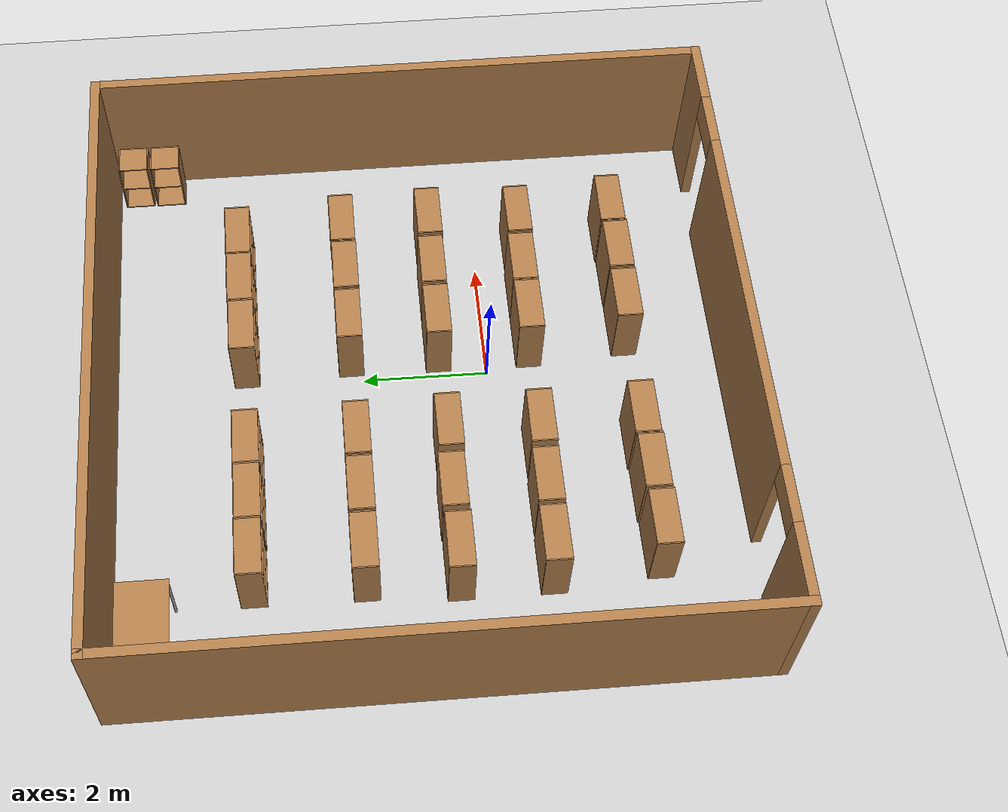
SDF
<sdf version="1.7">
 <world name="default">
  <light name="sun" type="directional">
   <pose>0 0 10 0 -0 0</pose>
   <diffuse>0.8 0.8 0.8 1</diffuse>
   <specular>0.2 0.2 0.2 1</specular>
   <attenuation>
    <range>1000</range>
    <constant>0.9</constant>
    <linear>0.01</linear>
    <quadratic>0.001</quadratic>
   </attenuation>
   <direction>-0.5 0.1 -0.9</direction>
   <spot><inner_angle>0</inner_angle><outer_angle>0</outer_angle><falloff>0</falloff></spot>
  </light>
  <model name="ground_plane">
   <static>1</static>
   <link name="link">
    <collision name="collision">
     <geometry><plane><normal>0 0 1</normal><size>100 100</size></plane></geometry>
     <surface>
      <contact><collide_bitmask>65535</collide_bitmask></contact>
      <friction><ode><mu>100</mu><mu2>50</mu2></ode></friction>
     </surface>
    </collision>
    <visual name="visual">
     <cast_shadows>0</cast_shadows>
     <geometry><plane><normal>0 0 1</normal><size>100 100</size></plane></geometry>
     <material>
      <script><uri>file://media/materials/scripts/gazebo.material</uri><name>Gazebo/Grey</name></script>
     </material>
    </visual>
   </link>
  </model>
  <gravity>0 0 -9.8</gravity>
  <magnetic_field>6e-06 2.3e-05 -4.2e-05</magnetic_field>
  <atmosphere type="adiabatic"/>
  <physics type="ode">
   <max_step_size>0.001</max_step_size>
   <real_time_factor>1</real_time_factor>
   <real_time_update_rate>1000</real_time_update_rate>
  </physics>
  <scene><ambient>0.4 0.4 0.4 1</ambient><background>0.7 0.7 0.7 1</background><shadows>1</shadows></scene>
  <audio><device>default</device></audio>
  <spherical_coordinates>
   <surface_model>EARTH_WGS84</surface_model>
   <latitude_deg>0</latitude_deg>
   <longitude_deg>0</longitude_deg>
   <elevation>0</elevation>
   <heading_deg>0</heading_deg>
  </spherical_coordinates>
  <model name="test">
   <pose>-0.47841 1.11325 0 0 -0 0</pose>
   <link name="Wall_13">
    <collision name="Wall_13_Collision">
     <geometry><box><size>10 0.15 2.5</size></box></geometry>
     <pose>0 0 1.25 0 -0 0</pose>
    </collision>
    <visual name="Wall_13_Visual">
     <pose>0 0 1.25 0 -0 0</pose>
     <geometry><box><size>10 0.15 2.5</size></box></geometry>
     <material>
      <script><uri>file://media/materials/scripts/gazebo.material</uri><name>Gazebo/Wood</name></script>
      <ambient>1 1 1 1</ambient>
     </material>
     <meta><layer>0</layer></meta>
    </visual>
    <pose>0 4.925 0 0 -0 0</pose>
   </link>
   <link name="Wall_14">
    <collision name="Wall_14_Collision">
     <geometry><box><size>10 0.15 2.5</size></box></geometry>
     <pose>0 0 1.25 0 -0 0</pose>
    </collision>
    <visual name="Wall_14_Visual">
     <pose>0 0 1.25 0 -0 0</pose>
     <geometry><box><size>10 0.15 2.5</size></box></geometry>
     <material>
      <script><uri>file://media/materials/scripts/gazebo.material</uri><name>Gazebo/Wood</name></script>
      <ambient>1 1 1 1</ambient>
     </material>
     <meta><layer>0</layer></meta>
    </visual>
    <pose>4.925 -0 0 0 -0 -1.5708</pose>
   </link>
   <link name="Wall_17">
    <collision name="Wall_17_Collision">
     <geometry><box><size>10 0.15 2.5</size></box></geometry>
     <pose>0 0 1.25 0 -0 0</pose>
    </collision>
    <visual name="Wall_17_Visual">
     <pose>0 0 1.25 0 -0 0</pose>
     <geometry><box><size>10 0.15 2.5</size></box></geometry>
     <material>
      <script><uri>file://media/materials/scripts/gazebo.material</uri><name>Gazebo/Wood</name></script>
      <ambient>1 1 1 1</ambient>
     </material>
     <meta><layer>0</layer></meta>
    </visual>
    <pose>-4.925 -0 0 0 -0 1.5708</pose>
   </link>
   <link name="Wall_5">
    <pose>0 -4.925 0 0 -0 3.14159</pose>
    <visual name="Wall_5_Visual_0">
     <pose>-4.45546 0 1.25 0 -0 0</pose>
     <geometry><box><size>1.08909 0.15 2.5</size></box></geometry>
     <material>
      <script><uri>file://media/materials/scripts/gazebo.material</uri><name>Gazebo/Wood</name></script>
      <ambient>1 1 1 1</ambient>
     </material>
     <meta><layer>0</layer></meta>
    </visual>
    <collision name="Wall_5_Collision_0">
     <geometry><box><size>1.08909 0.15 2.5</size></box></geometry>
     <pose>-4.45546 0 1.25 0 -0 0</pose>
    </collision>
    <visual name="Wall_5_Visual_1">
     <pose>-0.081777 0 1.25 0 -0 0</pose>
     <geometry><box><size>5.85827 0.15 2.5</size></box></geometry>
     <material>
      <script><uri>file://media/materials/scripts/gazebo.material</uri><name>Gazebo/Wood</name></script>
      <ambient>1 1 1 1</ambient>
     </material>
     <meta><layer>0</layer></meta>
    </visual>
    <collision name="Wall_5_Collision_1">
     <geometry><box><size>5.85827 0.15 2.5</size></box></geometry>
     <pose>-0.081777 0 1.25 0 -0 0</pose>
    </collision>
    <visual name="Wall_5_Visual_2">
     <pose>4.37368 0 1.25 0 -0 0</pose>
     <geometry><box><size>1.25264 0.15 2.5</size></box></geometry>
     <material>
      <script><uri>file://media/materials/scripts/gazebo.material</uri><name>Gazebo/Wood</name></script>
      <ambient>1 1 1 1</ambient>
     </material>
     <meta><layer>0</layer></meta>
    </visual>
    <collision name="Wall_5_Collision_2">
     <geometry><box><size>1.25264 0.15 2.5</size></box></geometry>
     <pose>4.37368 0 1.25 0 -0 0</pose>
    </collision>
    <visual name="Wall_5_Visual_3">
     <pose>-3.46091 0 2.25 0 -0 0</pose>
     <geometry><box><size>0.9 0.15 0.5</size></box></geometry>
     <material>
      <script><uri>file://media/materials/scripts/gazebo.material</uri><name>Gazebo/Wood</name></script>
      <ambient>1 1 1 1</ambient>
     </material>
     <meta><layer>0</layer></meta>
    </visual>
    <collision name="Wall_5_Collision_3">
     <geometry><box><size>0.9 0.15 0.5</size></box></geometry>
     <pose>-3.46091 0 2.25 0 -0 0</pose>
    </collision>
    <visual name="Wall_5_Visual_4">
     <pose>3.29736 0 2.25 0 -0 0</pose>
     <geometry><box><size>0.9 0.15 0.5</size></box></geometry>
     <material>
      <script><uri>file://media/materials/scripts/gazebo.material</uri><name>Gazebo/Wood</name></script>
      <ambient>1 1 1 1</ambient>
     </material>
     <meta><layer>0</layer></meta>
    </visual>
    <collision name="Wall_5_Collision_4">
     <geometry><box><size>0.9 0.15 0.5</size></box></geometry>
     <pose>3.29736 0 2.25 0 -0 0</pose>
    </collision>
   </link>
   <static>1</static>
  </model>
  <model name="bookshelf">
   <static>1</static>
   <link name="link">
    <inertial><mass>1</mass></inertial>
    <collision name="back">
     <pose>0 0.005 0.6 0 -0 0</pose>
     <geometry><box><size>0.9 0.01 1.2</size></box></geometry>
    </collision>
    <visual name="visual1">
     <pose>0 0.005 0.6 0 -0 0</pose>
     <geometry><box><size>0.9 0.01 1.2</size></box></geometry>
     <material>
      <script><uri>file://media/materials/scripts/gazebo.material</uri><name>Gazebo/Wood</name></script>
     </material>
    </visual>
    <collision name="left_side">
     <pose>0.45 -0.195 0.6 0 -0 0</pose>
     <geometry><box><size>0.02 0.4 1.2</size></box></geometry>
    </collision>
    <visual name="visual2">
     <pose>0.45 -0.195 0.6 0 -0 0</pose>
     <geometry><box><size>0.02 0.4 1.2</size></box></geometry>
     <material>
      <script><uri>file://media/materials/scripts/gazebo.material</uri><name>Gazebo/Wood</name></script>
     </material>
    </visual>
    <collision name="right_side">
     <pose>-0.45 -0.195 0.6 0 -0 0</pose>
     <geometry><box><size>0.02 0.4 1.2</size></box></geometry>
    </collision>
    <visual name="visual3">
     <pose>-0.45 -0.195 0.6 0 -0 0</pose>
     <geometry><box><size>0.02 0.4 1.2</size></box></geometry>
     <material>
      <script><uri>file://media/materials/scripts/gazebo.material</uri><name>Gazebo/Wood</name></script>
     </material>
    </visual>
    <collision name="bottom">
     <pose>0 -0.195 0.03 0 -0 0</pose>
     <geometry><box><size>0.88 0.4 0.06</size></box></geometry>
    </collision>
    <visual name="visual4">
     <pose>0 -0.195 0.03 0 -0 0</pose>
     <geometry><box><size>0.88 0.4 0.06</size></box></geometry>
     <material>
      <script><uri>file://media/materials/scripts/gazebo.material</uri><name>Gazebo/Wood</name></script>
     </material>
    </visual>
    <collision name="top">
     <pose>0 -0.195 1.19 0 -0 0</pose>
     <geometry><box><size>0.88 0.4 0.02</size></box></geometry>
    </collision>
    <visual name="visual5">
     <pose>0 -0.195 1.19 0 -0 0</pose>
     <geometry><box><size>0.88 0.4 0.02</size></box></geometry>
     <material>
      <script><uri>file://media/materials/scripts/gazebo.material</uri><name>Gazebo/Wood</name></script>
     </material>
    </visual>
    <collision name="low_shelf">
     <pose>0 -0.195 0.43 0 -0 0</pose>
     <geometry><box><size>0.88 0.4 0.02</size></box></geometry>
    </collision>
    <visual name="visual6">
     <pose>0 -0.195 0.43 0 -0 0</pose>
     <geometry><box><size>0.88 0.4 0.02</size></box></geometry>
     <material>
      <script><uri>file://media/materials/scripts/gazebo.material</uri><name>Gazebo/Wood</name></script>
     </material>
    </visual>
    <collision name="high_shelf">
     <pose>0 -0.195 0.8 0 -0 0</pose>
     <geometry><box><size>0.88 0.4 0.02</size></box></geometry>
    </collision>
    <visual name="visual7">
     <pose>0 -0.195 0.8 0 -0 0</pose>
     <geometry><box><size>0.88 0.4 0.02</size></box></geometry>
     <material>
      <script><uri>file://media/materials/scripts/gazebo.material</uri><name>Gazebo/Wood</name></script>
     </material>
    </visual>
   </link>
   <pose>-3.36376 4.05845 0 0 -0 0</pose>
  </model>
  <model name="bookshelf_0">
   <static>1</static>
   <link name="link">
    <inertial><mass>1</mass></inertial>
    <collision name="back">
     <pose>0 0.005 0.6 0 -0 0</pose>
     <geometry><box><size>0.9 0.01 1.2</size></box></geometry>
    </collision>
    <visual name="visual1">
     <pose>0 0.005 0.6 0 -0 0</pose>
     <geometry><box><size>0.9 0.01 1.2</size></box></geometry>
     <material>
      <script><uri>file://media/materials/scripts/gazebo.material</uri><name>Gazebo/Wood</name></script>
     </material>
    </visual>
    <collision name="left_side">
     <pose>0.45 -0.195 0.6 0 -0 0</pose>
     <geometry><box><size>0.02 0.4 1.2</size></box></geometry>
    </collision>
    <visual name="visual2">
     <pose>0.45 -0.195 0.6 0 -0 0</pose>
     <geometry><box><size>0.02 0.4 1.2</size></box></geometry>
     <material>
      <script><uri>file://media/materials/scripts/gazebo.material</uri><name>Gazebo/Wood</name></script>
     </material>
    </visual>
    <collision name="right_side">
     <pose>-0.45 -0.195 0.6 0 -0 0</pose>
     <geometry><box><size>0.02 0.4 1.2</size></box></geometry>
    </collision>
    <visual name="visual3">
     <pose>-0.45 -0.195 0.6 0 -0 0</pose>
     <geometry><box><size>0.02 0.4 1.2</size></box></geometry>
     <material>
      <script><uri>file://media/materials/scripts/gazebo.material</uri><name>Gazebo/Wood</name></script>
     </material>
    </visual>
    <collision name="bottom">
     <pose>0 -0.195 0.03 0 -0 0</pose>
     <geometry><box><size>0.88 0.4 0.06</size></box></geometry>
    </collision>
    <visual name="visual4">
     <pose>0 -0.195 0.03 0 -0 0</pose>
     <geometry><box><size>0.88 0.4 0.06</size></box></geometry>
     <material>
      <script><uri>file://media/materials/scripts/gazebo.material</uri><name>Gazebo/Wood</name></script>
     </material>
    </visual>
    <collision name="top">
     <pose>0 -0.195 1.19 0 -0 0</pose>
     <geometry><box><size>0.88 0.4 0.02</size></box></geometry>
    </collision>
    <visual name="visual5">
     <pose>0 -0.195 1.19 0 -0 0</pose>
     <geometry><box><size>0.88 0.4 0.02</size></box></geometry>
     <material>
      <script><uri>file://media/materials/scripts/gazebo.material</uri><name>Gazebo/Wood</name></script>
     </material>
    </visual>
    <collision name="low_shelf">
     <pose>0 -0.195 0.43 0 -0 0</pose>
     <geometry><box><size>0.88 0.4 0.02</size></box></geometry>
    </collision>
    <visual name="visual6">
     <pose>0 -0.195 0.43 0 -0 0</pose>
     <geometry><box><size>0.88 0.4 0.02</size></box></geometry>
     <material>
      <script><uri>file://media/materials/scripts/gazebo.material</uri><name>Gazebo/Wood</name></script>
     </material>
    </visual>
    <collision name="high_shelf">
     <pose>0 -0.195 0.8 0 -0 0</pose>
     <geometry><box><size>0.88 0.4 0.02</size></box></geometry>
    </collision>
    <visual name="visual7">
     <pose>0 -0.195 0.8 0 -0 0</pose>
     <geometry><box><size>0.88 0.4 0.02</size></box></geometry>
     <material>
      <script><uri>file://media/materials/scripts/gazebo.material</uri><name>Gazebo/Wood</name></script>
     </material>
    </visual>
   </link>
   <pose>-2.44784 4.05211 0 0 -0 0</pose>
  </model>
  <model name="bookshelf_1">
   <static>1</static>
   <link name="link">
    <inertial><mass>1</mass></inertial>
    <collision name="back">
     <pose>0 0.005 0.6 0 -0 0</pose>
     <geometry><box><size>0.9 0.01 1.2</size></box></geometry>
    </collision>
    <visual name="visual1">
     <pose>0 0.005 0.6 0 -0 0</pose>
     <geometry><box><size>0.9 0.01 1.2</size></box></geometry>
     <material>
      <script><uri>file://media/materials/scripts/gazebo.material</uri><name>Gazebo/Wood</name></script>
     </material>
    </visual>
    <collision name="left_side">
     <pose>0.45 -0.195 0.6 0 -0 0</pose>
     <geometry><box><size>0.02 0.4 1.2</size></box></geometry>
    </collision>
    <visual name="visual2">
     <pose>0.45 -0.195 0.6 0 -0 0</pose>
     <geometry><box><size>0.02 0.4 1.2</size></box></geometry>
     <material>
      <script><uri>file://media/materials/scripts/gazebo.material</uri><name>Gazebo/Wood</name></script>
     </material>
    </visual>
    <collision name="right_side">
     <pose>-0.45 -0.195 0.6 0 -0 0</pose>
     <geometry><box><size>0.02 0.4 1.2</size></box></geometry>
    </collision>
    <visual name="visual3">
     <pose>-0.45 -0.195 0.6 0 -0 0</pose>
     <geometry><box><size>0.02 0.4 1.2</size></box></geometry>
     <material>
      <script><uri>file://media/materials/scripts/gazebo.material</uri><name>Gazebo/Wood</name></script>
     </material>
    </visual>
    <collision name="bottom">
     <pose>0 -0.195 0.03 0 -0 0</pose>
     <geometry><box><size>0.88 0.4 0.06</size></box></geometry>
    </collision>
    <visual name="visual4">
     <pose>0 -0.195 0.03 0 -0 0</pose>
     <geometry><box><size>0.88 0.4 0.06</size></box></geometry>
     <material>
      <script><uri>file://media/materials/scripts/gazebo.material</uri><name>Gazebo/Wood</name></script>
     </material>
    </visual>
    <collision name="top">
     <pose>0 -0.195 1.19 0 -0 0</pose>
     <geometry><box><size>0.88 0.4 0.02</size></box></geometry>
    </collision>
    <visual name="visual5">
     <pose>0 -0.195 1.19 0 -0 0</pose>
     <geometry><box><size>0.88 0.4 0.02</size></box></geometry>
     <material>
      <script><uri>file://media/materials/scripts/gazebo.material</uri><name>Gazebo/Wood</name></script>
     </material>
    </visual>
    <collision name="low_shelf">
     <pose>0 -0.195 0.43 0 -0 0</pose>
     <geometry><box><size>0.88 0.4 0.02</size></box></geometry>
    </collision>
    <visual name="visual6">
     <pose>0 -0.195 0.43 0 -0 0</pose>
     <geometry><box><size>0.88 0.4 0.02</size></box></geometry>
     <material>
      <script><uri>file://media/materials/scripts/gazebo.material</uri><name>Gazebo/Wood</name></script>
     </material>
    </visual>
    <collision name="high_shelf">
     <pose>0 -0.195 0.8 0 -0 0</pose>
     <geometry><box><size>0.88 0.4 0.02</size></box></geometry>
    </collision>
    <visual name="visual7">
     <pose>0 -0.195 0.8 0 -0 0</pose>
     <geometry><box><size>0.88 0.4 0.02</size></box></geometry>
     <material>
      <script><uri>file://media/materials/scripts/gazebo.material</uri><name>Gazebo/Wood</name></script>
     </material>
    </visual>
   </link>
   <pose>-1.52934 4.05379 0 0 -0 0</pose>
  </model>
  <model name="bookshelf_2">
   <static>1</static>
   <link name="link">
    <inertial><mass>1</mass></inertial>
    <collision name="back">
     <pose>0 0.005 0.6 0 -0 0</pose>
     <geometry><box><size>0.9 0.01 1.2</size></box></geometry>
    </collision>
    <visual name="visual1">
     <pose>0 0.005 0.6 0 -0 0</pose>
     <geometry><box><size>0.9 0.01 1.2</size></box></geometry>
     <material>
      <script><uri>file://media/materials/scripts/gazebo.material</uri><name>Gazebo/Wood</name></script>
     </material>
    </visual>
    <collision name="left_side">
     <pose>0.45 -0.195 0.6 0 -0 0</pose>
     <geometry><box><size>0.02 0.4 1.2</size></box></geometry>
    </collision>
    <visual name="visual2">
     <pose>0.45 -0.195 0.6 0 -0 0</pose>
     <geometry><box><size>0.02 0.4 1.2</size></box></geometry>
     <material>
      <script><uri>file://media/materials/scripts/gazebo.material</uri><name>Gazebo/Wood</name></script>
     </material>
    </visual>
    <collision name="right_side">
     <pose>-0.45 -0.195 0.6 0 -0 0</pose>
     <geometry><box><size>0.02 0.4 1.2</size></box></geometry>
    </collision>
    <visual name="visual3">
     <pose>-0.45 -0.195 0.6 0 -0 0</pose>
     <geometry><box><size>0.02 0.4 1.2</size></box></geometry>
     <material>
      <script><uri>file://media/materials/scripts/gazebo.material</uri><name>Gazebo/Wood</name></script>
     </material>
    </visual>
    <collision name="bottom">
     <pose>0 -0.195 0.03 0 -0 0</pose>
     <geometry><box><size>0.88 0.4 0.06</size></box></geometry>
    </collision>
    <visual name="visual4">
     <pose>0 -0.195 0.03 0 -0 0</pose>
     <geometry><box><size>0.88 0.4 0.06</size></box></geometry>
     <material>
      <script><uri>file://media/materials/scripts/gazebo.material</uri><name>Gazebo/Wood</name></script>
     </material>
    </visual>
    <collision name="top">
     <pose>0 -0.195 1.19 0 -0 0</pose>
     <geometry><box><size>0.88 0.4 0.02</size></box></geometry>
    </collision>
    <visual name="visual5">
     <pose>0 -0.195 1.19 0 -0 0</pose>
     <geometry><box><size>0.88 0.4 0.02</size></box></geometry>
     <material>
      <script><uri>file://media/materials/scripts/gazebo.material</uri><name>Gazebo/Wood</name></script>
     </material>
    </visual>
    <collision name="low_shelf">
     <pose>0 -0.195 0.43 0 -0 0</pose>
     <geometry><box><size>0.88 0.4 0.02</size></box></geometry>
    </collision>
    <visual name="visual6">
     <pose>0 -0.195 0.43 0 -0 0</pose>
     <geometry><box><size>0.88 0.4 0.02</size></box></geometry>
     <material>
      <script><uri>file://media/materials/scripts/gazebo.material</uri><name>Gazebo/Wood</name></script>
     </material>
    </visual>
    <collision name="high_shelf">
     <pose>0 -0.195 0.8 0 -0 0</pose>
     <geometry><box><size>0.88 0.4 0.02</size></box></geometry>
    </collision>
    <visual name="visual7">
     <pose>0 -0.195 0.8 0 -0 0</pose>
     <geometry><box><size>0.88 0.4 0.02</size></box></geometry>
     <material>
      <script><uri>file://media/materials/scripts/gazebo.material</uri><name>Gazebo/Wood</name></script>
     </material>
    </visual>
   </link>
   <pose>0.490142 4.07229 0 0 -0 0</pose>
  </model>
  <model name="bookshelf_3">
   <static>1</static>
   <link name="link">
    <inertial><mass>1</mass></inertial>
    <collision name="back">
     <pose>0 0.005 0.6 0 -0 0</pose>
     <geometry><box><size>0.9 0.01 1.2</size></box></geometry>
    </collision>
    <visual name="visual1">
     <pose>0 0.005 0.6 0 -0 0</pose>
     <geometry><box><size>0.9 0.01 1.2</size></box></geometry>
     <material>
      <script><uri>file://media/materials/scripts/gazebo.material</uri><name>Gazebo/Wood</name></script>
     </material>
    </visual>
    <collision name="left_side">
     <pose>0.45 -0.195 0.6 0 -0 0</pose>
     <geometry><box><size>0.02 0.4 1.2</size></box></geometry>
    </collision>
    <visual name="visual2">
     <pose>0.45 -0.195 0.6 0 -0 0</pose>
     <geometry><box><size>0.02 0.4 1.2</size></box></geometry>
     <material>
      <script><uri>file://media/materials/scripts/gazebo.material</uri><name>Gazebo/Wood</name></script>
     </material>
    </visual>
    <collision name="right_side">
     <pose>-0.45 -0.195 0.6 0 -0 0</pose>
     <geometry><box><size>0.02 0.4 1.2</size></box></geometry>
    </collision>
    <visual name="visual3">
     <pose>-0.45 -0.195 0.6 0 -0 0</pose>
     <geometry><box><size>0.02 0.4 1.2</size></box></geometry>
     <material>
      <script><uri>file://media/materials/scripts/gazebo.material</uri><name>Gazebo/Wood</name></script>
     </material>
    </visual>
    <collision name="bottom">
     <pose>0 -0.195 0.03 0 -0 0</pose>
     <geometry><box><size>0.88 0.4 0.06</size></box></geometry>
    </collision>
    <visual name="visual4">
     <pose>0 -0.195 0.03 0 -0 0</pose>
     <geometry><box><size>0.88 0.4 0.06</size></box></geometry>
     <material>
      <script><uri>file://media/materials/scripts/gazebo.material</uri><name>Gazebo/Wood</name></script>
     </material>
    </visual>
    <collision name="top">
     <pose>0 -0.195 1.19 0 -0 0</pose>
     <geometry><box><size>0.88 0.4 0.02</size></box></geometry>
    </collision>
    <visual name="visual5">
     <pose>0 -0.195 1.19 0 -0 0</pose>
     <geometry><box><size>0.88 0.4 0.02</size></box></geometry>
     <material>
      <script><uri>file://media/materials/scripts/gazebo.material</uri><name>Gazebo/Wood</name></script>
     </material>
    </visual>
    <collision name="low_shelf">
     <pose>0 -0.195 0.43 0 -0 0</pose>
     <geometry><box><size>0.88 0.4 0.02</size></box></geometry>
    </collision>
    <visual name="visual6">
     <pose>0 -0.195 0.43 0 -0 0</pose>
     <geometry><box><size>0.88 0.4 0.02</size></box></geometry>
     <material>
      <script><uri>file://media/materials/scripts/gazebo.material</uri><name>Gazebo/Wood</name></script>
     </material>
    </visual>
    <collision name="high_shelf">
     <pose>0 -0.195 0.8 0 -0 0</pose>
     <geometry><box><size>0.88 0.4 0.02</size></box></geometry>
    </collision>
    <visual name="visual7">
     <pose>0 -0.195 0.8 0 -0 0</pose>
     <geometry><box><size>0.88 0.4 0.02</size></box></geometry>
     <material>
      <script><uri>file://media/materials/scripts/gazebo.material</uri><name>Gazebo/Wood</name></script>
     </material>
    </visual>
   </link>
   <pose>1.41244 4.08469 0 0 -0 0</pose>
  </model>
  <model name="bookshelf_4">
   <static>1</static>
   <link name="link">
    <inertial><mass>1</mass></inertial>
    <collision name="back">
     <pose>0 0.005 0.6 0 -0 0</pose>
     <geometry><box><size>0.9 0.01 1.2</size></box></geometry>
    </collision>
    <visual name="visual1">
     <pose>0 0.005 0.6 0 -0 0</pose>
     <geometry><box><size>0.9 0.01 1.2</size></box></geometry>
     <material>
      <script><uri>file://media/materials/scripts/gazebo.material</uri><name>Gazebo/Wood</name></script>
     </material>
    </visual>
    <collision name="left_side">
     <pose>0.45 -0.195 0.6 0 -0 0</pose>
     <geometry><box><size>0.02 0.4 1.2</size></box></geometry>
    </collision>
    <visual name="visual2">
     <pose>0.45 -0.195 0.6 0 -0 0</pose>
     <geometry><box><size>0.02 0.4 1.2</size></box></geometry>
     <material>
      <script><uri>file://media/materials/scripts/gazebo.material</uri><name>Gazebo/Wood</name></script>
     </material>
    </visual>
    <collision name="right_side">
     <pose>-0.45 -0.195 0.6 0 -0 0</pose>
     <geometry><box><size>0.02 0.4 1.2</size></box></geometry>
    </collision>
    <visual name="visual3">
     <pose>-0.45 -0.195 0.6 0 -0 0</pose>
     <geometry><box><size>0.02 0.4 1.2</size></box></geometry>
     <material>
      <script><uri>file://media/materials/scripts/gazebo.material</uri><name>Gazebo/Wood</name></script>
     </material>
    </visual>
    <collision name="bottom">
     <pose>0 -0.195 0.03 0 -0 0</pose>
     <geometry><box><size>0.88 0.4 0.06</size></box></geometry>
    </collision>
    <visual name="visual4">
     <pose>0 -0.195 0.03 0 -0 0</pose>
     <geometry><box><size>0.88 0.4 0.06</size></box></geometry>
     <material>
      <script><uri>file://media/materials/scripts/gazebo.material</uri><name>Gazebo/Wood</name></script>
     </material>
    </visual>
    <collision name="top">
     <pose>0 -0.195 1.19 0 -0 0</pose>
     <geometry><box><size>0.88 0.4 0.02</size></box></geometry>
    </collision>
    <visual name="visual5">
     <pose>0 -0.195 1.19 0 -0 0</pose>
     <geometry><box><size>0.88 0.4 0.02</size></box></geometry>
     <material>
      <script><uri>file://media/materials/scripts/gazebo.material</uri><name>Gazebo/Wood</name></script>
     </material>
    </visual>
    <collision name="low_shelf">
     <pose>0 -0.195 0.43 0 -0 0</pose>
     <geometry><box><size>0.88 0.4 0.02</size></box></geometry>
    </collision>
    <visual name="visual6">
     <pose>0 -0.195 0.43 0 -0 0</pose>
     <geometry><box><size>0.88 0.4 0.02</size></box></geometry>
     <material>
      <script><uri>file://media/materials/scripts/gazebo.material</uri><name>Gazebo/Wood</name></script>
     </material>
    </visual>
    <collision name="high_shelf">
     <pose>0 -0.195 0.8 0 -0 0</pose>
     <geometry><box><size>0.88 0.4 0.02</size></box></geometry>
    </collision>
    <visual name="visual7">
     <pose>0 -0.195 0.8 0 -0 0</pose>
     <geometry><box><size>0.88 0.4 0.02</size></box></geometry>
     <material>
      <script><uri>file://media/materials/scripts/gazebo.material</uri><name>Gazebo/Wood</name></script>
     </material>
    </visual>
   </link>
   <pose>2.32485 4.08963 0 0 -0 0</pose>
  </model>
  <model name="bookshelf_5">
   <static>1</static>
   <link name="link">
    <inertial><mass>1</mass></inertial>
    <collision name="back">
     <pose>0 0.005 0.6 0 -0 0</pose>
     <geometry><box><size>0.9 0.01 1.2</size></box></geometry>
    </collision>
    <visual name="visual1">
     <pose>0 0.005 0.6 0 -0 0</pose>
     <geometry><box><size>0.9 0.01 1.2</size></box></geometry>
     <material>
      <script><uri>file://media/materials/scripts/gazebo.material</uri><name>Gazebo/Wood</name></script>
     </material>
    </visual>
    <collision name="left_side">
     <pose>0.45 -0.195 0.6 0 -0 0</pose>
     <geometry><box><size>0.02 0.4 1.2</size></box></geometry>
    </collision>
    <visual name="visual2">
     <pose>0.45 -0.195 0.6 0 -0 0</pose>
     <geometry><box><size>0.02 0.4 1.2</size></box></geometry>
     <material>
      <script><uri>file://media/materials/scripts/gazebo.material</uri><name>Gazebo/Wood</name></script>
     </material>
    </visual>
    <collision name="right_side">
     <pose>-0.45 -0.195 0.6 0 -0 0</pose>
     <geometry><box><size>0.02 0.4 1.2</size></box></geometry>
    </collision>
    <visual name="visual3">
     <pose>-0.45 -0.195 0.6 0 -0 0</pose>
     <geometry><box><size>0.02 0.4 1.2</size></box></geometry>
     <material>
      <script><uri>file://media/materials/scripts/gazebo.material</uri><name>Gazebo/Wood</name></script>
     </material>
    </visual>
    <collision name="bottom">
     <pose>0 -0.195 0.03 0 -0 0</pose>
     <geometry><box><size>0.88 0.4 0.06</size></box></geometry>
    </collision>
    <visual name="visual4">
     <pose>0 -0.195 0.03 0 -0 0</pose>
     <geometry><box><size>0.88 0.4 0.06</size></box></geometry>
     <material>
      <script><uri>file://media/materials/scripts/gazebo.material</uri><name>Gazebo/Wood</name></script>
     </material>
    </visual>
    <collision name="top">
     <pose>0 -0.195 1.19 0 -0 0</pose>
     <geometry><box><size>0.88 0.4 0.02</size></box></geometry>
    </collision>
    <visual name="visual5">
     <pose>0 -0.195 1.19 0 -0 0</pose>
     <geometry><box><size>0.88 0.4 0.02</size></box></geometry>
     <material>
      <script><uri>file://media/materials/scripts/gazebo.material</uri><name>Gazebo/Wood</name></script>
     </material>
    </visual>
    <collision name="low_shelf">
     <pose>0 -0.195 0.43 0 -0 0</pose>
     <geometry><box><size>0.88 0.4 0.02</size></box></geometry>
    </collision>
    <visual name="visual6">
     <pose>0 -0.195 0.43 0 -0 0</pose>
     <geometry><box><size>0.88 0.4 0.02</size></box></geometry>
     <material>
      <script><uri>file://media/materials/scripts/gazebo.material</uri><name>Gazebo/Wood</name></script>
     </material>
    </visual>
    <collision name="high_shelf">
     <pose>0 -0.195 0.8 0 -0 0</pose>
     <geometry><box><size>0.88 0.4 0.02</size></box></geometry>
    </collision>
    <visual name="visual7">
     <pose>0 -0.195 0.8 0 -0 0</pose>
     <geometry><box><size>0.88 0.4 0.02</size></box></geometry>
     <material>
      <script><uri>file://media/materials/scripts/gazebo.material</uri><name>Gazebo/Wood</name></script>
     </material>
    </visual>
   </link>
   <pose>2.45061 2.38707 0 0 -0 0</pose>
  </model>
  <model name="bookshelf_6">
   <static>1</static>
   <link name="link">
    <inertial><mass>1</mass></inertial>
    <collision name="back">
     <pose>0 0.005 0.6 0 -0 0</pose>
     <geometry><box><size>0.9 0.01 1.2</size></box></geometry>
    </collision>
    <visual name="visual1">
     <pose>0 0.005 0.6 0 -0 0</pose>
     <geometry><box><size>0.9 0.01 1.2</size></box></geometry>
     <material>
      <script><uri>file://media/materials/scripts/gazebo.material</uri><name>Gazebo/Wood</name></script>
     </material>
    </visual>
    <collision name="left_side">
     <pose>0.45 -0.195 0.6 0 -0 0</pose>
     <geometry><box><size>0.02 0.4 1.2</size></box></geometry>
    </collision>
    <visual name="visual2">
     <pose>0.45 -0.195 0.6 0 -0 0</pose>
     <geometry><box><size>0.02 0.4 1.2</size></box></geometry>
     <material>
      <script><uri>file://media/materials/scripts/gazebo.material</uri><name>Gazebo/Wood</name></script>
     </material>
    </visual>
    <collision name="right_side">
     <pose>-0.45 -0.195 0.6 0 -0 0</pose>
     <geometry><box><size>0.02 0.4 1.2</size></box></geometry>
    </collision>
    <visual name="visual3">
     <pose>-0.45 -0.195 0.6 0 -0 0</pose>
     <geometry><box><size>0.02 0.4 1.2</size></box></geometry>
     <material>
      <script><uri>file://media/materials/scripts/gazebo.material</uri><name>Gazebo/Wood</name></script>
     </material>
    </visual>
    <collision name="bottom">
     <pose>0 -0.195 0.03 0 -0 0</pose>
     <geometry><box><size>0.88 0.4 0.06</size></box></geometry>
    </collision>
    <visual name="visual4">
     <pose>0 -0.195 0.03 0 -0 0</pose>
     <geometry><box><size>0.88 0.4 0.06</size></box></geometry>
     <material>
      <script><uri>file://media/materials/scripts/gazebo.material</uri><name>Gazebo/Wood</name></script>
     </material>
    </visual>
    <collision name="top">
     <pose>0 -0.195 1.19 0 -0 0</pose>
     <geometry><box><size>0.88 0.4 0.02</size></box></geometry>
    </collision>
    <visual name="visual5">
     <pose>0 -0.195 1.19 0 -0 0</pose>
     <geometry><box><size>0.88 0.4 0.02</size></box></geometry>
     <material>
      <script><uri>file://media/materials/scripts/gazebo.material</uri><name>Gazebo/Wood</name></script>
     </material>
    </visual>
    <collision name="low_shelf">
     <pose>0 -0.195 0.43 0 -0 0</pose>
     <geometry><box><size>0.88 0.4 0.02</size></box></geometry>
    </collision>
    <visual name="visual6">
     <pose>0 -0.195 0.43 0 -0 0</pose>
     <geometry><box><size>0.88 0.4 0.02</size></box></geometry>
     <material>
      <script><uri>file://media/materials/scripts/gazebo.material</uri><name>Gazebo/Wood</name></script>
     </material>
    </visual>
    <collision name="high_shelf">
     <pose>0 -0.195 0.8 0 -0 0</pose>
     <geometry><box><size>0.88 0.4 0.02</size></box></geometry>
    </collision>
    <visual name="visual7">
     <pose>0 -0.195 0.8 0 -0 0</pose>
     <geometry><box><size>0.88 0.4 0.02</size></box></geometry>
     <material>
      <script><uri>file://media/materials/scripts/gazebo.material</uri><name>Gazebo/Wood</name></script>
     </material>
    </visual>
   </link>
   <pose>1.51879 2.37897 0 0 -0 0</pose>
  </model>
  <model name="bookshelf_7">
   <static>1</static>
   <link name="link">
    <inertial><mass>1</mass></inertial>
    <collision name="back">
     <pose>0 0.005 0.6 0 -0 0</pose>
     <geometry><box><size>0.9 0.01 1.2</size></box></geometry>
    </collision>
    <visual name="visual1">
     <pose>0 0.005 0.6 0 -0 0</pose>
     <geometry><box><size>0.9 0.01 1.2</size></box></geometry>
     <material>
      <script><uri>file://media/materials/scripts/gazebo.material</uri><name>Gazebo/Wood</name></script>
     </material>
    </visual>
    <collision name="left_side">
     <pose>0.45 -0.195 0.6 0 -0 0</pose>
     <geometry><box><size>0.02 0.4 1.2</size></box></geometry>
    </collision>
    <visual name="visual2">
     <pose>0.45 -0.195 0.6 0 -0 0</pose>
     <geometry><box><size>0.02 0.4 1.2</size></box></geometry>
     <material>
      <script><uri>file://media/materials/scripts/gazebo.material</uri><name>Gazebo/Wood</name></script>
     </material>
    </visual>
    <collision name="right_side">
     <pose>-0.45 -0.195 0.6 0 -0 0</pose>
     <geometry><box><size>0.02 0.4 1.2</size></box></geometry>
    </collision>
    <visual name="visual3">
     <pose>-0.45 -0.195 0.6 0 -0 0</pose>
     <geometry><box><size>0.02 0.4 1.2</size></box></geometry>
     <material>
      <script><uri>file://media/materials/scripts/gazebo.material</uri><name>Gazebo/Wood</name></script>
     </material>
    </visual>
    <collision name="bottom">
     <pose>0 -0.195 0.03 0 -0 0</pose>
     <geometry><box><size>0.88 0.4 0.06</size></box></geometry>
    </collision>
    <visual name="visual4">
     <pose>0 -0.195 0.03 0 -0 0</pose>
     <geometry><box><size>0.88 0.4 0.06</size></box></geometry>
     <material>
      <script><uri>file://media/materials/scripts/gazebo.material</uri><name>Gazebo/Wood</name></script>
     </material>
    </visual>
    <collision name="top">
     <pose>0 -0.195 1.19 0 -0 0</pose>
     <geometry><box><size>0.88 0.4 0.02</size></box></geometry>
    </collision>
    <visual name="visual5">
     <pose>0 -0.195 1.19 0 -0 0</pose>
     <geometry><box><size>0.88 0.4 0.02</size></box></geometry>
     <material>
      <script><uri>file://media/materials/scripts/gazebo.material</uri><name>Gazebo/Wood</name></script>
     </material>
    </visual>
    <collision name="low_shelf">
     <pose>0 -0.195 0.43 0 -0 0</pose>
     <geometry><box><size>0.88 0.4 0.02</size></box></geometry>
    </collision>
    <visual name="visual6">
     <pose>0 -0.195 0.43 0 -0 0</pose>
     <geometry><box><size>0.88 0.4 0.02</size></box></geometry>
     <material>
      <script><uri>file://media/materials/scripts/gazebo.material</uri><name>Gazebo/Wood</name></script>
     </material>
    </visual>
    <collision name="high_shelf">
     <pose>0 -0.195 0.8 0 -0 0</pose>
     <geometry><box><size>0.88 0.4 0.02</size></box></geometry>
    </collision>
    <visual name="visual7">
     <pose>0 -0.195 0.8 0 -0 0</pose>
     <geometry><box><size>0.88 0.4 0.02</size></box></geometry>
     <material>
      <script><uri>file://media/materials/scripts/gazebo.material</uri><name>Gazebo/Wood</name></script>
     </material>
    </visual>
   </link>
   <pose>0.574777 2.38083 0 0 -0 0</pose>
  </model>
  <model name="bookshelf_8">
   <static>1</static>
   <link name="link">
    <inertial><mass>1</mass></inertial>
    <collision name="back">
     <pose>0 0.005 0.6 0 -0 0</pose>
     <geometry><box><size>0.9 0.01 1.2</size></box></geometry>
    </collision>
    <visual name="visual1">
     <pose>0 0.005 0.6 0 -0 0</pose>
     <geometry><box><size>0.9 0.01 1.2</size></box></geometry>
     <material>
      <script><uri>file://media/materials/scripts/gazebo.material</uri><name>Gazebo/Wood</name></script>
     </material>
    </visual>
    <collision name="left_side">
     <pose>0.45 -0.195 0.6 0 -0 0</pose>
     <geometry><box><size>0.02 0.4 1.2</size></box></geometry>
    </collision>
    <visual name="visual2">
     <pose>0.45 -0.195 0.6 0 -0 0</pose>
     <geometry><box><size>0.02 0.4 1.2</size></box></geometry>
     <material>
      <script><uri>file://media/materials/scripts/gazebo.material</uri><name>Gazebo/Wood</name></script>
     </material>
    </visual>
    <collision name="right_side">
     <pose>-0.45 -0.195 0.6 0 -0 0</pose>
     <geometry><box><size>0.02 0.4 1.2</size></box></geometry>
    </collision>
    <visual name="visual3">
     <pose>-0.45 -0.195 0.6 0 -0 0</pose>
     <geometry><box><size>0.02 0.4 1.2</size></box></geometry>
     <material>
      <script><uri>file://media/materials/scripts/gazebo.material</uri><name>Gazebo/Wood</name></script>
     </material>
    </visual>
    <collision name="bottom">
     <pose>0 -0.195 0.03 0 -0 0</pose>
     <geometry><box><size>0.88 0.4 0.06</size></box></geometry>
    </collision>
    <visual name="visual4">
     <pose>0 -0.195 0.03 0 -0 0</pose>
     <geometry><box><size>0.88 0.4 0.06</size></box></geometry>
     <material>
      <script><uri>file://media/materials/scripts/gazebo.material</uri><name>Gazebo/Wood</name></script>
     </material>
    </visual>
    <collision name="top">
     <pose>0 -0.195 1.19 0 -0 0</pose>
     <geometry><box><size>0.88 0.4 0.02</size></box></geometry>
    </collision>
    <visual name="visual5">
     <pose>0 -0.195 1.19 0 -0 0</pose>
     <geometry><box><size>0.88 0.4 0.02</size></box></geometry>
     <material>
      <script><uri>file://media/materials/scripts/gazebo.material</uri><name>Gazebo/Wood</name></script>
     </material>
    </visual>
    <collision name="low_shelf">
     <pose>0 -0.195 0.43 0 -0 0</pose>
     <geometry><box><size>0.88 0.4 0.02</size></box></geometry>
    </collision>
    <visual name="visual6">
     <pose>0 -0.195 0.43 0 -0 0</pose>
     <geometry><box><size>0.88 0.4 0.02</size></box></geometry>
     <material>
      <script><uri>file://media/materials/scripts/gazebo.material</uri><name>Gazebo/Wood</name></script>
     </material>
    </visual>
    <collision name="high_shelf">
     <pose>0 -0.195 0.8 0 -0 0</pose>
     <geometry><box><size>0.88 0.4 0.02</size></box></geometry>
    </collision>
    <visual name="visual7">
     <pose>0 -0.195 0.8 0 -0 0</pose>
     <geometry><box><size>0.88 0.4 0.02</size></box></geometry>
     <material>
      <script><uri>file://media/materials/scripts/gazebo.material</uri><name>Gazebo/Wood</name></script>
     </material>
    </visual>
   </link>
   <pose>-1.50236 2.36105 0 0 -0 0</pose>
  </model>
  <model name="bookshelf_9">
   <static>1</static>
   <link name="link">
    <inertial><mass>1</mass></inertial>
    <collision name="back">
     <pose>0 0.005 0.6 0 -0 0</pose>
     <geometry><box><size>0.9 0.01 1.2</size></box></geometry>
    </collision>
    <visual name="visual1">
     <pose>0 0.005 0.6 0 -0 0</pose>
     <geometry><box><size>0.9 0.01 1.2</size></box></geometry>
     <material>
      <script><uri>file://media/materials/scripts/gazebo.material</uri><name>Gazebo/Wood</name></script>
     </material>
    </visual>
    <collision name="left_side">
     <pose>0.45 -0.195 0.6 0 -0 0</pose>
     <geometry><box><size>0.02 0.4 1.2</size></box></geometry>
    </collision>
    <visual name="visual2">
     <pose>0.45 -0.195 0.6 0 -0 0</pose>
     <geometry><box><size>0.02 0.4 1.2</size></box></geometry>
     <material>
      <script><uri>file://media/materials/scripts/gazebo.material</uri><name>Gazebo/Wood</name></script>
     </material>
    </visual>
    <collision name="right_side">
     <pose>-0.45 -0.195 0.6 0 -0 0</pose>
     <geometry><box><size>0.02 0.4 1.2</size></box></geometry>
    </collision>
    <visual name="visual3">
     <pose>-0.45 -0.195 0.6 0 -0 0</pose>
     <geometry><box><size>0.02 0.4 1.2</size></box></geometry>
     <material>
      <script><uri>file://media/materials/scripts/gazebo.material</uri><name>Gazebo/Wood</name></script>
     </material>
    </visual>
    <collision name="bottom">
     <pose>0 -0.195 0.03 0 -0 0</pose>
     <geometry><box><size>0.88 0.4 0.06</size></box></geometry>
    </collision>
    <visual name="visual4">
     <pose>0 -0.195 0.03 0 -0 0</pose>
     <geometry><box><size>0.88 0.4 0.06</size></box></geometry>
     <material>
      <script><uri>file://media/materials/scripts/gazebo.material</uri><name>Gazebo/Wood</name></script>
     </material>
    </visual>
    <collision name="top">
     <pose>0 -0.195 1.19 0 -0 0</pose>
     <geometry><box><size>0.88 0.4 0.02</size></box></geometry>
    </collision>
    <visual name="visual5">
     <pose>0 -0.195 1.19 0 -0 0</pose>
     <geometry><box><size>0.88 0.4 0.02</size></box></geometry>
     <material>
      <script><uri>file://media/materials/scripts/gazebo.material</uri><name>Gazebo/Wood</name></script>
     </material>
    </visual>
    <collision name="low_shelf">
     <pose>0 -0.195 0.43 0 -0 0</pose>
     <geometry><box><size>0.88 0.4 0.02</size></box></geometry>
    </collision>
    <visual name="visual6">
     <pose>0 -0.195 0.43 0 -0 0</pose>
     <geometry><box><size>0.88 0.4 0.02</size></box></geometry>
     <material>
      <script><uri>file://media/materials/scripts/gazebo.material</uri><name>Gazebo/Wood</name></script>
     </material>
    </visual>
    <collision name="high_shelf">
     <pose>0 -0.195 0.8 0 -0 0</pose>
     <geometry><box><size>0.88 0.4 0.02</size></box></geometry>
    </collision>
    <visual name="visual7">
     <pose>0 -0.195 0.8 0 -0 0</pose>
     <geometry><box><size>0.88 0.4 0.02</size></box></geometry>
     <material>
      <script><uri>file://media/materials/scripts/gazebo.material</uri><name>Gazebo/Wood</name></script>
     </material>
    </visual>
   </link>
   <pose>-2.44539 2.36269 0 0 -0 0</pose>
  </model>
  <model name="bookshelf_10">
   <static>1</static>
   <link name="link">
    <inertial><mass>1</mass></inertial>
    <collision name="back">
     <pose>0 0.005 0.6 0 -0 0</pose>
     <geometry><box><size>0.9 0.01 1.2</size></box></geometry>
    </collision>
    <visual name="visual1">
     <pose>0 0.005 0.6 0 -0 0</pose>
     <geometry><box><size>0.9 0.01 1.2</size></box></geometry>
     <material>
      <script><uri>file://media/materials/scripts/gazebo.material</uri><name>Gazebo/Wood</name></script>
     </material>
    </visual>
    <collision name="left_side">
     <pose>0.45 -0.195 0.6 0 -0 0</pose>
     <geometry><box><size>0.02 0.4 1.2</size></box></geometry>
    </collision>
    <visual name="visual2">
     <pose>0.45 -0.195 0.6 0 -0 0</pose>
     <geometry><box><size>0.02 0.4 1.2</size></box></geometry>
     <material>
      <script><uri>file://media/materials/scripts/gazebo.material</uri><name>Gazebo/Wood</name></script>
     </material>
    </visual>
    <collision name="right_side">
     <pose>-0.45 -0.195 0.6 0 -0 0</pose>
     <geometry><box><size>0.02 0.4 1.2</size></box></geometry>
    </collision>
    <visual name="visual3">
     <pose>-0.45 -0.195 0.6 0 -0 0</pose>
     <geometry><box><size>0.02 0.4 1.2</size></box></geometry>
     <material>
      <script><uri>file://media/materials/scripts/gazebo.material</uri><name>Gazebo/Wood</name></script>
     </material>
    </visual>
    <collision name="bottom">
     <pose>0 -0.195 0.03 0 -0 0</pose>
     <geometry><box><size>0.88 0.4 0.06</size></box></geometry>
    </collision>
    <visual name="visual4">
     <pose>0 -0.195 0.03 0 -0 0</pose>
     <geometry><box><size>0.88 0.4 0.06</size></box></geometry>
     <material>
      <script><uri>file://media/materials/scripts/gazebo.material</uri><name>Gazebo/Wood</name></script>
     </material>
    </visual>
    <collision name="top">
     <pose>0 -0.195 1.19 0 -0 0</pose>
     <geometry><box><size>0.88 0.4 0.02</size></box></geometry>
    </collision>
    <visual name="visual5">
     <pose>0 -0.195 1.19 0 -0 0</pose>
     <geometry><box><size>0.88 0.4 0.02</size></box></geometry>
     <material>
      <script><uri>file://media/materials/scripts/gazebo.material</uri><name>Gazebo/Wood</name></script>
     </material>
    </visual>
    <collision name="low_shelf">
     <pose>0 -0.195 0.43 0 -0 0</pose>
     <geometry><box><size>0.88 0.4 0.02</size></box></geometry>
    </collision>
    <visual name="visual6">
     <pose>0 -0.195 0.43 0 -0 0</pose>
     <geometry><box><size>0.88 0.4 0.02</size></box></geometry>
     <material>
      <script><uri>file://media/materials/scripts/gazebo.material</uri><name>Gazebo/Wood</name></script>
     </material>
    </visual>
    <collision name="high_shelf">
     <pose>0 -0.195 0.8 0 -0 0</pose>
     <geometry><box><size>0.88 0.4 0.02</size></box></geometry>
    </collision>
    <visual name="visual7">
     <pose>0 -0.195 0.8 0 -0 0</pose>
     <geometry><box><size>0.88 0.4 0.02</size></box></geometry>
     <material>
      <script><uri>file://media/materials/scripts/gazebo.material</uri><name>Gazebo/Wood</name></script>
     </material>
    </visual>
   </link>
   <pose>-3.39073 2.36423 0 0 -0 0</pose>
  </model>
  <model name="bookshelf_11">
   <static>1</static>
   <link name="link">
    <inertial><mass>1</mass></inertial>
    <collision name="back">
     <pose>0 0.005 0.6 0 -0 0</pose>
     <geometry><box><size>0.9 0.01 1.2</size></box></geometry>
    </collision>
    <visual name="visual1">
     <pose>0 0.005 0.6 0 -0 0</pose>
     <geometry><box><size>0.9 0.01 1.2</size></box></geometry>
     <material>
      <script><uri>file://media/materials/scripts/gazebo.material</uri><name>Gazebo/Wood</name></script>
     </material>
    </visual>
    <collision name="left_side">
     <pose>0.45 -0.195 0.6 0 -0 0</pose>
     <geometry><box><size>0.02 0.4 1.2</size></box></geometry>
    </collision>
    <visual name="visual2">
     <pose>0.45 -0.195 0.6 0 -0 0</pose>
     <geometry><box><size>0.02 0.4 1.2</size></box></geometry>
     <material>
      <script><uri>file://media/materials/scripts/gazebo.material</uri><name>Gazebo/Wood</name></script>
     </material>
    </visual>
    <collision name="right_side">
     <pose>-0.45 -0.195 0.6 0 -0 0</pose>
     <geometry><box><size>0.02 0.4 1.2</size></box></geometry>
    </collision>
    <visual name="visual3">
     <pose>-0.45 -0.195 0.6 0 -0 0</pose>
     <geometry><box><size>0.02 0.4 1.2</size></box></geometry>
     <material>
      <script><uri>file://media/materials/scripts/gazebo.material</uri><name>Gazebo/Wood</name></script>
     </material>
    </visual>
    <collision name="bottom">
     <pose>0 -0.195 0.03 0 -0 0</pose>
     <geometry><box><size>0.88 0.4 0.06</size></box></geometry>
    </collision>
    <visual name="visual4">
     <pose>0 -0.195 0.03 0 -0 0</pose>
     <geometry><box><size>0.88 0.4 0.06</size></box></geometry>
     <material>
      <script><uri>file://media/materials/scripts/gazebo.material</uri><name>Gazebo/Wood</name></script>
     </material>
    </visual>
    <collision name="top">
     <pose>0 -0.195 1.19 0 -0 0</pose>
     <geometry><box><size>0.88 0.4 0.02</size></box></geometry>
    </collision>
    <visual name="visual5">
     <pose>0 -0.195 1.19 0 -0 0</pose>
     <geometry><box><size>0.88 0.4 0.02</size></box></geometry>
     <material>
      <script><uri>file://media/materials/scripts/gazebo.material</uri><name>Gazebo/Wood</name></script>
     </material>
    </visual>
    <collision name="low_shelf">
     <pose>0 -0.195 0.43 0 -0 0</pose>
     <geometry><box><size>0.88 0.4 0.02</size></box></geometry>
    </collision>
    <visual name="visual6">
     <pose>0 -0.195 0.43 0 -0 0</pose>
     <geometry><box><size>0.88 0.4 0.02</size></box></geometry>
     <material>
      <script><uri>file://media/materials/scripts/gazebo.material</uri><name>Gazebo/Wood</name></script>
     </material>
    </visual>
    <collision name="high_shelf">
     <pose>0 -0.195 0.8 0 -0 0</pose>
     <geometry><box><size>0.88 0.4 0.02</size></box></geometry>
    </collision>
    <visual name="visual7">
     <pose>0 -0.195 0.8 0 -0 0</pose>
     <geometry><box><size>0.88 0.4 0.02</size></box></geometry>
     <material>
      <script><uri>file://media/materials/scripts/gazebo.material</uri><name>Gazebo/Wood</name></script>
     </material>
    </visual>
   </link>
   <pose>-3.48659 0.963539 0 0 -0 0</pose>
  </model>
  <model name="bookshelf_12">
   <static>1</static>
   <link name="link">
    <inertial><mass>1</mass></inertial>
    <collision name="back">
     <pose>0 0.005 0.6 0 -0 0</pose>
     <geometry><box><size>0.9 0.01 1.2</size></box></geometry>
    </collision>
    <visual name="visual1">
     <pose>0 0.005 0.6 0 -0 0</pose>
     <geometry><box><size>0.9 0.01 1.2</size></box></geometry>
     <material>
      <script><uri>file://media/materials/scripts/gazebo.material</uri><name>Gazebo/Wood</name></script>
     </material>
    </visual>
    <collision name="left_side">
     <pose>0.45 -0.195 0.6 0 -0 0</pose>
     <geometry><box><size>0.02 0.4 1.2</size></box></geometry>
    </collision>
    <visual name="visual2">
     <pose>0.45 -0.195 0.6 0 -0 0</pose>
     <geometry><box><size>0.02 0.4 1.2</size></box></geometry>
     <material>
      <script><uri>file://media/materials/scripts/gazebo.material</uri><name>Gazebo/Wood</name></script>
     </material>
    </visual>
    <collision name="right_side">
     <pose>-0.45 -0.195 0.6 0 -0 0</pose>
     <geometry><box><size>0.02 0.4 1.2</size></box></geometry>
    </collision>
    <visual name="visual3">
     <pose>-0.45 -0.195 0.6 0 -0 0</pose>
     <geometry><box><size>0.02 0.4 1.2</size></box></geometry>
     <material>
      <script><uri>file://media/materials/scripts/gazebo.material</uri><name>Gazebo/Wood</name></script>
     </material>
    </visual>
    <collision name="bottom">
     <pose>0 -0.195 0.03 0 -0 0</pose>
     <geometry><box><size>0.88 0.4 0.06</size></box></geometry>
    </collision>
    <visual name="visual4">
     <pose>0 -0.195 0.03 0 -0 0</pose>
     <geometry><box><size>0.88 0.4 0.06</size></box></geometry>
     <material>
      <script><uri>file://media/materials/scripts/gazebo.material</uri><name>Gazebo/Wood</name></script>
     </material>
    </visual>
    <collision name="top">
     <pose>0 -0.195 1.19 0 -0 0</pose>
     <geometry><box><size>0.88 0.4 0.02</size></box></geometry>
    </collision>
    <visual name="visual5">
     <pose>0 -0.195 1.19 0 -0 0</pose>
     <geometry><box><size>0.88 0.4 0.02</size></box></geometry>
     <material>
      <script><uri>file://media/materials/scripts/gazebo.material</uri><name>Gazebo/Wood</name></script>
     </material>
    </visual>
    <collision name="low_shelf">
     <pose>0 -0.195 0.43 0 -0 0</pose>
     <geometry><box><size>0.88 0.4 0.02</size></box></geometry>
    </collision>
    <visual name="visual6">
     <pose>0 -0.195 0.43 0 -0 0</pose>
     <geometry><box><size>0.88 0.4 0.02</size></box></geometry>
     <material>
      <script><uri>file://media/materials/scripts/gazebo.material</uri><name>Gazebo/Wood</name></script>
     </material>
    </visual>
    <collision name="high_shelf">
     <pose>0 -0.195 0.8 0 -0 0</pose>
     <geometry><box><size>0.88 0.4 0.02</size></box></geometry>
    </collision>
    <visual name="visual7">
     <pose>0 -0.195 0.8 0 -0 0</pose>
     <geometry><box><size>0.88 0.4 0.02</size></box></geometry>
     <material>
      <script><uri>file://media/materials/scripts/gazebo.material</uri><name>Gazebo/Wood</name></script>
     </material>
    </visual>
   </link>
   <pose>-2.48969 0.976329 0 0 -0 0</pose>
  </model>
  <model name="bookshelf_13">
   <static>1</static>
   <link name="link">
    <inertial><mass>1</mass></inertial>
    <collision name="back">
     <pose>0 0.005 0.6 0 -0 0</pose>
     <geometry><box><size>0.9 0.01 1.2</size></box></geometry>
    </collision>
    <visual name="visual1">
     <pose>0 0.005 0.6 0 -0 0</pose>
     <geometry><box><size>0.9 0.01 1.2</size></box></geometry>
     <material>
      <script><uri>file://media/materials/scripts/gazebo.material</uri><name>Gazebo/Wood</name></script>
     </material>
    </visual>
    <collision name="left_side">
     <pose>0.45 -0.195 0.6 0 -0 0</pose>
     <geometry><box><size>0.02 0.4 1.2</size></box></geometry>
    </collision>
    <visual name="visual2">
     <pose>0.45 -0.195 0.6 0 -0 0</pose>
     <geometry><box><size>0.02 0.4 1.2</size></box></geometry>
     <material>
      <script><uri>file://media/materials/scripts/gazebo.material</uri><name>Gazebo/Wood</name></script>
     </material>
    </visual>
    <collision name="right_side">
     <pose>-0.45 -0.195 0.6 0 -0 0</pose>
     <geometry><box><size>0.02 0.4 1.2</size></box></geometry>
    </collision>
    <visual name="visual3">
     <pose>-0.45 -0.195 0.6 0 -0 0</pose>
     <geometry><box><size>0.02 0.4 1.2</size></box></geometry>
     <material>
      <script><uri>file://media/materials/scripts/gazebo.material</uri><name>Gazebo/Wood</name></script>
     </material>
    </visual>
    <collision name="bottom">
     <pose>0 -0.195 0.03 0 -0 0</pose>
     <geometry><box><size>0.88 0.4 0.06</size></box></geometry>
    </collision>
    <visual name="visual4">
     <pose>0 -0.195 0.03 0 -0 0</pose>
     <geometry><box><size>0.88 0.4 0.06</size></box></geometry>
     <material>
      <script><uri>file://media/materials/scripts/gazebo.material</uri><name>Gazebo/Wood</name></script>
     </material>
    </visual>
    <collision name="top">
     <pose>0 -0.195 1.19 0 -0 0</pose>
     <geometry><box><size>0.88 0.4 0.02</size></box></geometry>
    </collision>
    <visual name="visual5">
     <pose>0 -0.195 1.19 0 -0 0</pose>
     <geometry><box><size>0.88 0.4 0.02</size></box></geometry>
     <material>
      <script><uri>file://media/materials/scripts/gazebo.material</uri><name>Gazebo/Wood</name></script>
     </material>
    </visual>
    <collision name="low_shelf">
     <pose>0 -0.195 0.43 0 -0 0</pose>
     <geometry><box><size>0.88 0.4 0.02</size></box></geometry>
    </collision>
    <visual name="visual6">
     <pose>0 -0.195 0.43 0 -0 0</pose>
     <geometry><box><size>0.88 0.4 0.02</size></box></geometry>
     <material>
      <script><uri>file://media/materials/scripts/gazebo.material</uri><name>Gazebo/Wood</name></script>
     </material>
    </visual>
    <collision name="high_shelf">
     <pose>0 -0.195 0.8 0 -0 0</pose>
     <geometry><box><size>0.88 0.4 0.02</size></box></geometry>
    </collision>
    <visual name="visual7">
     <pose>0 -0.195 0.8 0 -0 0</pose>
     <geometry><box><size>0.88 0.4 0.02</size></box></geometry>
     <material>
      <script><uri>file://media/materials/scripts/gazebo.material</uri><name>Gazebo/Wood</name></script>
     </material>
    </visual>
   </link>
   <pose>-1.47176 0.953052 0 0 -0 0</pose>
  </model>
  <model name="bookshelf_14">
   <static>1</static>
   <link name="link">
    <inertial><mass>1</mass></inertial>
    <collision name="back">
     <pose>0 0.005 0.6 0 -0 0</pose>
     <geometry><box><size>0.9 0.01 1.2</size></box></geometry>
    </collision>
    <visual name="visual1">
     <pose>0 0.005 0.6 0 -0 0</pose>
     <geometry><box><size>0.9 0.01 1.2</size></box></geometry>
     <material>
      <script><uri>file://media/materials/scripts/gazebo.material</uri><name>Gazebo/Wood</name></script>
     </material>
    </visual>
    <collision name="left_side">
     <pose>0.45 -0.195 0.6 0 -0 0</pose>
     <geometry><box><size>0.02 0.4 1.2</size></box></geometry>
    </collision>
    <visual name="visual2">
     <pose>0.45 -0.195 0.6 0 -0 0</pose>
     <geometry><box><size>0.02 0.4 1.2</size></box></geometry>
     <material>
      <script><uri>file://media/materials/scripts/gazebo.material</uri><name>Gazebo/Wood</name></script>
     </material>
    </visual>
    <collision name="right_side">
     <pose>-0.45 -0.195 0.6 0 -0 0</pose>
     <geometry><box><size>0.02 0.4 1.2</size></box></geometry>
    </collision>
    <visual name="visual3">
     <pose>-0.45 -0.195 0.6 0 -0 0</pose>
     <geometry><box><size>0.02 0.4 1.2</size></box></geometry>
     <material>
      <script><uri>file://media/materials/scripts/gazebo.material</uri><name>Gazebo/Wood</name></script>
     </material>
    </visual>
    <collision name="bottom">
     <pose>0 -0.195 0.03 0 -0 0</pose>
     <geometry><box><size>0.88 0.4 0.06</size></box></geometry>
    </collision>
    <visual name="visual4">
     <pose>0 -0.195 0.03 0 -0 0</pose>
     <geometry><box><size>0.88 0.4 0.06</size></box></geometry>
     <material>
      <script><uri>file://media/materials/scripts/gazebo.material</uri><name>Gazebo/Wood</name></script>
     </material>
    </visual>
    <collision name="top">
     <pose>0 -0.195 1.19 0 -0 0</pose>
     <geometry><box><size>0.88 0.4 0.02</size></box></geometry>
    </collision>
    <visual name="visual5">
     <pose>0 -0.195 1.19 0 -0 0</pose>
     <geometry><box><size>0.88 0.4 0.02</size></box></geometry>
     <material>
      <script><uri>file://media/materials/scripts/gazebo.material</uri><name>Gazebo/Wood</name></script>
     </material>
    </visual>
    <collision name="low_shelf">
     <pose>0 -0.195 0.43 0 -0 0</pose>
     <geometry><box><size>0.88 0.4 0.02</size></box></geometry>
    </collision>
    <visual name="visual6">
     <pose>0 -0.195 0.43 0 -0 0</pose>
     <geometry><box><size>0.88 0.4 0.02</size></box></geometry>
     <material>
      <script><uri>file://media/materials/scripts/gazebo.material</uri><name>Gazebo/Wood</name></script>
     </material>
    </visual>
    <collision name="high_shelf">
     <pose>0 -0.195 0.8 0 -0 0</pose>
     <geometry><box><size>0.88 0.4 0.02</size></box></geometry>
    </collision>
    <visual name="visual7">
     <pose>0 -0.195 0.8 0 -0 0</pose>
     <geometry><box><size>0.88 0.4 0.02</size></box></geometry>
     <material>
      <script><uri>file://media/materials/scripts/gazebo.material</uri><name>Gazebo/Wood</name></script>
     </material>
    </visual>
   </link>
   <pose>0.555802 0.970865 0 0 -0 0</pose>
  </model>
  <model name="bookshelf_15">
   <static>1</static>
   <link name="link">
    <inertial><mass>1</mass></inertial>
    <collision name="back">
     <pose>0 0.005 0.6 0 -0 0</pose>
     <geometry><box><size>0.9 0.01 1.2</size></box></geometry>
    </collision>
    <visual name="visual1">
     <pose>0 0.005 0.6 0 -0 0</pose>
     <geometry><box><size>0.9 0.01 1.2</size></box></geometry>
     <material>
      <script><uri>file://media/materials/scripts/gazebo.material</uri><name>Gazebo/Wood</name></script>
     </material>
    </visual>
    <collision name="left_side">
     <pose>0.45 -0.195 0.6 0 -0 0</pose>
     <geometry><box><size>0.02 0.4 1.2</size></box></geometry>
    </collision>
    <visual name="visual2">
     <pose>0.45 -0.195 0.6 0 -0 0</pose>
     <geometry><box><size>0.02 0.4 1.2</size></box></geometry>
     <material>
      <script><uri>file://media/materials/scripts/gazebo.material</uri><name>Gazebo/Wood</name></script>
     </material>
    </visual>
    <collision name="right_side">
     <pose>-0.45 -0.195 0.6 0 -0 0</pose>
     <geometry><box><size>0.02 0.4 1.2</size></box></geometry>
    </collision>
    <visual name="visual3">
     <pose>-0.45 -0.195 0.6 0 -0 0</pose>
     <geometry><box><size>0.02 0.4 1.2</size></box></geometry>
     <material>
      <script><uri>file://media/materials/scripts/gazebo.material</uri><name>Gazebo/Wood</name></script>
     </material>
    </visual>
    <collision name="bottom">
     <pose>0 -0.195 0.03 0 -0 0</pose>
     <geometry><box><size>0.88 0.4 0.06</size></box></geometry>
    </collision>
    <visual name="visual4">
     <pose>0 -0.195 0.03 0 -0 0</pose>
     <geometry><box><size>0.88 0.4 0.06</size></box></geometry>
     <material>
      <script><uri>file://media/materials/scripts/gazebo.material</uri><name>Gazebo/Wood</name></script>
     </material>
    </visual>
    <collision name="top">
     <pose>0 -0.195 1.19 0 -0 0</pose>
     <geometry><box><size>0.88 0.4 0.02</size></box></geometry>
    </collision>
    <visual name="visual5">
     <pose>0 -0.195 1.19 0 -0 0</pose>
     <geometry><box><size>0.88 0.4 0.02</size></box></geometry>
     <material>
      <script><uri>file://media/materials/scripts/gazebo.material</uri><name>Gazebo/Wood</name></script>
     </material>
    </visual>
    <collision name="low_shelf">
     <pose>0 -0.195 0.43 0 -0 0</pose>
     <geometry><box><size>0.88 0.4 0.02</size></box></geometry>
    </collision>
    <visual name="visual6">
     <pose>0 -0.195 0.43 0 -0 0</pose>
     <geometry><box><size>0.88 0.4 0.02</size></box></geometry>
     <material>
      <script><uri>file://media/materials/scripts/gazebo.material</uri><name>Gazebo/Wood</name></script>
     </material>
    </visual>
    <collision name="high_shelf">
     <pose>0 -0.195 0.8 0 -0 0</pose>
     <geometry><box><size>0.88 0.4 0.02</size></box></geometry>
    </collision>
    <visual name="visual7">
     <pose>0 -0.195 0.8 0 -0 0</pose>
     <geometry><box><size>0.88 0.4 0.02</size></box></geometry>
     <material>
      <script><uri>file://media/materials/scripts/gazebo.material</uri><name>Gazebo/Wood</name></script>
     </material>
    </visual>
   </link>
   <pose>1.51844 0.970182 0 0 -0 0</pose>
  </model>
  <model name="bookshelf_16">
   <static>1</static>
   <link name="link">
    <inertial><mass>1</mass></inertial>
    <collision name="back">
     <pose>0 0.005 0.6 0 -0 0</pose>
     <geometry><box><size>0.9 0.01 1.2</size></box></geometry>
    </collision>
    <visual name="visual1">
     <pose>0 0.005 0.6 0 -0 0</pose>
     <geometry><box><size>0.9 0.01 1.2</size></box></geometry>
     <material>
      <script><uri>file://media/materials/scripts/gazebo.material</uri><name>Gazebo/Wood</name></script>
     </material>
    </visual>
    <collision name="left_side">
     <pose>0.45 -0.195 0.6 0 -0 0</pose>
     <geometry><box><size>0.02 0.4 1.2</size></box></geometry>
    </collision>
    <visual name="visual2">
     <pose>0.45 -0.195 0.6 0 -0 0</pose>
     <geometry><box><size>0.02 0.4 1.2</size></box></geometry>
     <material>
      <script><uri>file://media/materials/scripts/gazebo.material</uri><name>Gazebo/Wood</name></script>
     </material>
    </visual>
    <collision name="right_side">
     <pose>-0.45 -0.195 0.6 0 -0 0</pose>
     <geometry><box><size>0.02 0.4 1.2</size></box></geometry>
    </collision>
    <visual name="visual3">
     <pose>-0.45 -0.195 0.6 0 -0 0</pose>
     <geometry><box><size>0.02 0.4 1.2</size></box></geometry>
     <material>
      <script><uri>file://media/materials/scripts/gazebo.material</uri><name>Gazebo/Wood</name></script>
     </material>
    </visual>
    <collision name="bottom">
     <pose>0 -0.195 0.03 0 -0 0</pose>
     <geometry><box><size>0.88 0.4 0.06</size></box></geometry>
    </collision>
    <visual name="visual4">
     <pose>0 -0.195 0.03 0 -0 0</pose>
     <geometry><box><size>0.88 0.4 0.06</size></box></geometry>
     <material>
      <script><uri>file://media/materials/scripts/gazebo.material</uri><name>Gazebo/Wood</name></script>
     </material>
    </visual>
    <collision name="top">
     <pose>0 -0.195 1.19 0 -0 0</pose>
     <geometry><box><size>0.88 0.4 0.02</size></box></geometry>
    </collision>
    <visual name="visual5">
     <pose>0 -0.195 1.19 0 -0 0</pose>
     <geometry><box><size>0.88 0.4 0.02</size></box></geometry>
     <material>
      <script><uri>file://media/materials/scripts/gazebo.material</uri><name>Gazebo/Wood</name></script>
     </material>
    </visual>
    <collision name="low_shelf">
     <pose>0 -0.195 0.43 0 -0 0</pose>
     <geometry><box><size>0.88 0.4 0.02</size></box></geometry>
    </collision>
    <visual name="visual6">
     <pose>0 -0.195 0.43 0 -0 0</pose>
     <geometry><box><size>0.88 0.4 0.02</size></box></geometry>
     <material>
      <script><uri>file://media/materials/scripts/gazebo.material</uri><name>Gazebo/Wood</name></script>
     </material>
    </visual>
    <collision name="high_shelf">
     <pose>0 -0.195 0.8 0 -0 0</pose>
     <geometry><box><size>0.88 0.4 0.02</size></box></geometry>
    </collision>
    <visual name="visual7">
     <pose>0 -0.195 0.8 0 -0 0</pose>
     <geometry><box><size>0.88 0.4 0.02</size></box></geometry>
     <material>
      <script><uri>file://media/materials/scripts/gazebo.material</uri><name>Gazebo/Wood</name></script>
     </material>
    </visual>
   </link>
   <pose>2.48494 0.958079 0 0 -0 0</pose>
  </model>
  <model name="bookshelf_17">
   <static>1</static>
   <link name="link">
    <inertial><mass>1</mass></inertial>
    <collision name="back">
     <pose>0 0.005 0.6 0 -0 0</pose>
     <geometry><box><size>0.9 0.01 1.2</size></box></geometry>
    </collision>
    <visual name="visual1">
     <pose>0 0.005 0.6 0 -0 0</pose>
     <geometry><box><size>0.9 0.01 1.2</size></box></geometry>
     <material>
      <script><uri>file://media/materials/scripts/gazebo.material</uri><name>Gazebo/Wood</name></script>
     </material>
    </visual>
    <collision name="left_side">
     <pose>0.45 -0.195 0.6 0 -0 0</pose>
     <geometry><box><size>0.02 0.4 1.2</size></box></geometry>
    </collision>
    <visual name="visual2">
     <pose>0.45 -0.195 0.6 0 -0 0</pose>
     <geometry><box><size>0.02 0.4 1.2</size></box></geometry>
     <material>
      <script><uri>file://media/materials/scripts/gazebo.material</uri><name>Gazebo/Wood</name></script>
     </material>
    </visual>
    <collision name="right_side">
     <pose>-0.45 -0.195 0.6 0 -0 0</pose>
     <geometry><box><size>0.02 0.4 1.2</size></box></geometry>
    </collision>
    <visual name="visual3">
     <pose>-0.45 -0.195 0.6 0 -0 0</pose>
     <geometry><box><size>0.02 0.4 1.2</size></box></geometry>
     <material>
      <script><uri>file://media/materials/scripts/gazebo.material</uri><name>Gazebo/Wood</name></script>
     </material>
    </visual>
    <collision name="bottom">
     <pose>0 -0.195 0.03 0 -0 0</pose>
     <geometry><box><size>0.88 0.4 0.06</size></box></geometry>
    </collision>
    <visual name="visual4">
     <pose>0 -0.195 0.03 0 -0 0</pose>
     <geometry><box><size>0.88 0.4 0.06</size></box></geometry>
     <material>
      <script><uri>file://media/materials/scripts/gazebo.material</uri><name>Gazebo/Wood</name></script>
     </material>
    </visual>
    <collision name="top">
     <pose>0 -0.195 1.19 0 -0 0</pose>
     <geometry><box><size>0.88 0.4 0.02</size></box></geometry>
    </collision>
    <visual name="visual5">
     <pose>0 -0.195 1.19 0 -0 0</pose>
     <geometry><box><size>0.88 0.4 0.02</size></box></geometry>
     <material>
      <script><uri>file://media/materials/scripts/gazebo.material</uri><name>Gazebo/Wood</name></script>
     </material>
    </visual>
    <collision name="low_shelf">
     <pose>0 -0.195 0.43 0 -0 0</pose>
     <geometry><box><size>0.88 0.4 0.02</size></box></geometry>
    </collision>
    <visual name="visual6">
     <pose>0 -0.195 0.43 0 -0 0</pose>
     <geometry><box><size>0.88 0.4 0.02</size></box></geometry>
     <material>
      <script><uri>file://media/materials/scripts/gazebo.material</uri><name>Gazebo/Wood</name></script>
     </material>
    </visual>
    <collision name="high_shelf">
     <pose>0 -0.195 0.8 0 -0 0</pose>
     <geometry><box><size>0.88 0.4 0.02</size></box></geometry>
    </collision>
    <visual name="visual7">
     <pose>0 -0.195 0.8 0 -0 0</pose>
     <geometry><box><size>0.88 0.4 0.02</size></box></geometry>
     <material>
      <script><uri>file://media/materials/scripts/gazebo.material</uri><name>Gazebo/Wood</name></script>
     </material>
    </visual>
   </link>
   <pose>-3.48671 -0.442995 0 0 -0 0</pose>
  </model>
  <model name="bookshelf_18">
   <static>1</static>
   <link name="link">
    <inertial><mass>1</mass></inertial>
    <collision name="back">
     <pose>0 0.005 0.6 0 -0 0</pose>
     <geometry><box><size>0.9 0.01 1.2</size></box></geometry>
    </collision>
    <visual name="visual1">
     <pose>0 0.005 0.6 0 -0 0</pose>
     <geometry><box><size>0.9 0.01 1.2</size></box></geometry>
     <material>
      <script><uri>file://media/materials/scripts/gazebo.material</uri><name>Gazebo/Wood</name></script>
     </material>
    </visual>
    <collision name="left_side">
     <pose>0.45 -0.195 0.6 0 -0 0</pose>
     <geometry><box><size>0.02 0.4 1.2</size></box></geometry>
    </collision>
    <visual name="visual2">
     <pose>0.45 -0.195 0.6 0 -0 0</pose>
     <geometry><box><size>0.02 0.4 1.2</size></box></geometry>
     <material>
      <script><uri>file://media/materials/scripts/gazebo.material</uri><name>Gazebo/Wood</name></script>
     </material>
    </visual>
    <collision name="right_side">
     <pose>-0.45 -0.195 0.6 0 -0 0</pose>
     <geometry><box><size>0.02 0.4 1.2</size></box></geometry>
    </collision>
    <visual name="visual3">
     <pose>-0.45 -0.195 0.6 0 -0 0</pose>
     <geometry><box><size>0.02 0.4 1.2</size></box></geometry>
     <material>
      <script><uri>file://media/materials/scripts/gazebo.material</uri><name>Gazebo/Wood</name></script>
     </material>
    </visual>
    <collision name="bottom">
     <pose>0 -0.195 0.03 0 -0 0</pose>
     <geometry><box><size>0.88 0.4 0.06</size></box></geometry>
    </collision>
    <visual name="visual4">
     <pose>0 -0.195 0.03 0 -0 0</pose>
     <geometry><box><size>0.88 0.4 0.06</size></box></geometry>
     <material>
      <script><uri>file://media/materials/scripts/gazebo.material</uri><name>Gazebo/Wood</name></script>
     </material>
    </visual>
    <collision name="top">
     <pose>0 -0.195 1.19 0 -0 0</pose>
     <geometry><box><size>0.88 0.4 0.02</size></box></geometry>
    </collision>
    <visual name="visual5">
     <pose>0 -0.195 1.19 0 -0 0</pose>
     <geometry><box><size>0.88 0.4 0.02</size></box></geometry>
     <material>
      <script><uri>file://media/materials/scripts/gazebo.material</uri><name>Gazebo/Wood</name></script>
     </material>
    </visual>
    <collision name="low_shelf">
     <pose>0 -0.195 0.43 0 -0 0</pose>
     <geometry><box><size>0.88 0.4 0.02</size></box></geometry>
    </collision>
    <visual name="visual6">
     <pose>0 -0.195 0.43 0 -0 0</pose>
     <geometry><box><size>0.88 0.4 0.02</size></box></geometry>
     <material>
      <script><uri>file://media/materials/scripts/gazebo.material</uri><name>Gazebo/Wood</name></script>
     </material>
    </visual>
    <collision name="high_shelf">
     <pose>0 -0.195 0.8 0 -0 0</pose>
     <geometry><box><size>0.88 0.4 0.02</size></box></geometry>
    </collision>
    <visual name="visual7">
     <pose>0 -0.195 0.8 0 -0 0</pose>
     <geometry><box><size>0.88 0.4 0.02</size></box></geometry>
     <material>
      <script><uri>file://media/materials/scripts/gazebo.material</uri><name>Gazebo/Wood</name></script>
     </material>
    </visual>
   </link>
   <pose>-2.5153 -0.447156 0 0 -0 0</pose>
  </model>
  <model name="bookshelf_19">
   <static>1</static>
   <link name="link">
    <inertial><mass>1</mass></inertial>
    <collision name="back">
     <pose>0 0.005 0.6 0 -0 0</pose>
     <geometry><box><size>0.9 0.01 1.2</size></box></geometry>
    </collision>
    <visual name="visual1">
     <pose>0 0.005 0.6 0 -0 0</pose>
     <geometry><box><size>0.9 0.01 1.2</size></box></geometry>
     <material>
      <script><uri>file://media/materials/scripts/gazebo.material</uri><name>Gazebo/Wood</name></script>
     </material>
    </visual>
    <collision name="left_side">
     <pose>0.45 -0.195 0.6 0 -0 0</pose>
     <geometry><box><size>0.02 0.4 1.2</size></box></geometry>
    </collision>
    <visual name="visual2">
     <pose>0.45 -0.195 0.6 0 -0 0</pose>
     <geometry><box><size>0.02 0.4 1.2</size></box></geometry>
     <material>
      <script><uri>file://media/materials/scripts/gazebo.material</uri><name>Gazebo/Wood</name></script>
     </material>
    </visual>
    <collision name="right_side">
     <pose>-0.45 -0.195 0.6 0 -0 0</pose>
     <geometry><box><size>0.02 0.4 1.2</size></box></geometry>
    </collision>
    <visual name="visual3">
     <pose>-0.45 -0.195 0.6 0 -0 0</pose>
     <geometry><box><size>0.02 0.4 1.2</size></box></geometry>
     <material>
      <script><uri>file://media/materials/scripts/gazebo.material</uri><name>Gazebo/Wood</name></script>
     </material>
    </visual>
    <collision name="bottom">
     <pose>0 -0.195 0.03 0 -0 0</pose>
     <geometry><box><size>0.88 0.4 0.06</size></box></geometry>
    </collision>
    <visual name="visual4">
     <pose>0 -0.195 0.03 0 -0 0</pose>
     <geometry><box><size>0.88 0.4 0.06</size></box></geometry>
     <material>
      <script><uri>file://media/materials/scripts/gazebo.material</uri><name>Gazebo/Wood</name></script>
     </material>
    </visual>
    <collision name="top">
     <pose>0 -0.195 1.19 0 -0 0</pose>
     <geometry><box><size>0.88 0.4 0.02</size></box></geometry>
    </collision>
    <visual name="visual5">
     <pose>0 -0.195 1.19 0 -0 0</pose>
     <geometry><box><size>0.88 0.4 0.02</size></box></geometry>
     <material>
      <script><uri>file://media/materials/scripts/gazebo.material</uri><name>Gazebo/Wood</name></script>
     </material>
    </visual>
    <collision name="low_shelf">
     <pose>0 -0.195 0.43 0 -0 0</pose>
     <geometry><box><size>0.88 0.4 0.02</size></box></geometry>
    </collision>
    <visual name="visual6">
     <pose>0 -0.195 0.43 0 -0 0</pose>
     <geometry><box><size>0.88 0.4 0.02</size></box></geometry>
     <material>
      <script><uri>file://media/materials/scripts/gazebo.material</uri><name>Gazebo/Wood</name></script>
     </material>
    </visual>
    <collision name="high_shelf">
     <pose>0 -0.195 0.8 0 -0 0</pose>
     <geometry><box><size>0.88 0.4 0.02</size></box></geometry>
    </collision>
    <visual name="visual7">
     <pose>0 -0.195 0.8 0 -0 0</pose>
     <geometry><box><size>0.88 0.4 0.02</size></box></geometry>
     <material>
      <script><uri>file://media/materials/scripts/gazebo.material</uri><name>Gazebo/Wood</name></script>
     </material>
    </visual>
   </link>
   <pose>-1.50921 -0.459183 0 0 -0 0</pose>
  </model>
  <model name="bookshelf_20">
   <static>1</static>
   <link name="link">
    <inertial><mass>1</mass></inertial>
    <collision name="back">
     <pose>0 0.005 0.6 0 -0 0</pose>
     <geometry><box><size>0.9 0.01 1.2</size></box></geometry>
    </collision>
    <visual name="visual1">
     <pose>0 0.005 0.6 0 -0 0</pose>
     <geometry><box><size>0.9 0.01 1.2</size></box></geometry>
     <material>
      <script><uri>file://media/materials/scripts/gazebo.material</uri><name>Gazebo/Wood</name></script>
     </material>
    </visual>
    <collision name="left_side">
     <pose>0.45 -0.195 0.6 0 -0 0</pose>
     <geometry><box><size>0.02 0.4 1.2</size></box></geometry>
    </collision>
    <visual name="visual2">
     <pose>0.45 -0.195 0.6 0 -0 0</pose>
     <geometry><box><size>0.02 0.4 1.2</size></box></geometry>
     <material>
      <script><uri>file://media/materials/scripts/gazebo.material</uri><name>Gazebo/Wood</name></script>
     </material>
    </visual>
    <collision name="right_side">
     <pose>-0.45 -0.195 0.6 0 -0 0</pose>
     <geometry><box><size>0.02 0.4 1.2</size></box></geometry>
    </collision>
    <visual name="visual3">
     <pose>-0.45 -0.195 0.6 0 -0 0</pose>
     <geometry><box><size>0.02 0.4 1.2</size></box></geometry>
     <material>
      <script><uri>file://media/materials/scripts/gazebo.material</uri><name>Gazebo/Wood</name></script>
     </material>
    </visual>
    <collision name="bottom">
     <pose>0 -0.195 0.03 0 -0 0</pose>
     <geometry><box><size>0.88 0.4 0.06</size></box></geometry>
    </collision>
    <visual name="visual4">
     <pose>0 -0.195 0.03 0 -0 0</pose>
     <geometry><box><size>0.88 0.4 0.06</size></box></geometry>
     <material>
      <script><uri>file://media/materials/scripts/gazebo.material</uri><name>Gazebo/Wood</name></script>
     </material>
    </visual>
    <collision name="top">
     <pose>0 -0.195 1.19 0 -0 0</pose>
     <geometry><box><size>0.88 0.4 0.02</size></box></geometry>
    </collision>
    <visual name="visual5">
     <pose>0 -0.195 1.19 0 -0 0</pose>
     <geometry><box><size>0.88 0.4 0.02</size></box></geometry>
     <material>
      <script><uri>file://media/materials/scripts/gazebo.material</uri><name>Gazebo/Wood</name></script>
     </material>
    </visual>
    <collision name="low_shelf">
     <pose>0 -0.195 0.43 0 -0 0</pose>
     <geometry><box><size>0.88 0.4 0.02</size></box></geometry>
    </collision>
    <visual name="visual6">
     <pose>0 -0.195 0.43 0 -0 0</pose>
     <geometry><box><size>0.88 0.4 0.02</size></box></geometry>
     <material>
      <script><uri>file://media/materials/scripts/gazebo.material</uri><name>Gazebo/Wood</name></script>
     </material>
    </visual>
    <collision name="high_shelf">
     <pose>0 -0.195 0.8 0 -0 0</pose>
     <geometry><box><size>0.88 0.4 0.02</size></box></geometry>
    </collision>
    <visual name="visual7">
     <pose>0 -0.195 0.8 0 -0 0</pose>
     <geometry><box><size>0.88 0.4 0.02</size></box></geometry>
     <material>
      <script><uri>file://media/materials/scripts/gazebo.material</uri><name>Gazebo/Wood</name></script>
     </material>
    </visual>
   </link>
   <pose>0.536006 -0.494316 0 0 -0 0</pose>
  </model>
  <model name="bookshelf_21">
   <static>1</static>
   <link name="link">
    <inertial><mass>1</mass></inertial>
    <collision name="back">
     <pose>0 0.005 0.6 0 -0 0</pose>
     <geometry><box><size>0.9 0.01 1.2</size></box></geometry>
    </collision>
    <visual name="visual1">
     <pose>0 0.005 0.6 0 -0 0</pose>
     <geometry><box><size>0.9 0.01 1.2</size></box></geometry>
     <material>
      <script><uri>file://media/materials/scripts/gazebo.material</uri><name>Gazebo/Wood</name></script>
     </material>
    </visual>
    <collision name="left_side">
     <pose>0.45 -0.195 0.6 0 -0 0</pose>
     <geometry><box><size>0.02 0.4 1.2</size></box></geometry>
    </collision>
    <visual name="visual2">
     <pose>0.45 -0.195 0.6 0 -0 0</pose>
     <geometry><box><size>0.02 0.4 1.2</size></box></geometry>
     <material>
      <script><uri>file://media/materials/scripts/gazebo.material</uri><name>Gazebo/Wood</name></script>
     </material>
    </visual>
    <collision name="right_side">
     <pose>-0.45 -0.195 0.6 0 -0 0</pose>
     <geometry><box><size>0.02 0.4 1.2</size></box></geometry>
    </collision>
    <visual name="visual3">
     <pose>-0.45 -0.195 0.6 0 -0 0</pose>
     <geometry><box><size>0.02 0.4 1.2</size></box></geometry>
     <material>
      <script><uri>file://media/materials/scripts/gazebo.material</uri><name>Gazebo/Wood</name></script>
     </material>
    </visual>
    <collision name="bottom">
     <pose>0 -0.195 0.03 0 -0 0</pose>
     <geometry><box><size>0.88 0.4 0.06</size></box></geometry>
    </collision>
    <visual name="visual4">
     <pose>0 -0.195 0.03 0 -0 0</pose>
     <geometry><box><size>0.88 0.4 0.06</size></box></geometry>
     <material>
      <script><uri>file://media/materials/scripts/gazebo.material</uri><name>Gazebo/Wood</name></script>
     </material>
    </visual>
    <collision name="top">
     <pose>0 -0.195 1.19 0 -0 0</pose>
     <geometry><box><size>0.88 0.4 0.02</size></box></geometry>
    </collision>
    <visual name="visual5">
     <pose>0 -0.195 1.19 0 -0 0</pose>
     <geometry><box><size>0.88 0.4 0.02</size></box></geometry>
     <material>
      <script><uri>file://media/materials/scripts/gazebo.material</uri><name>Gazebo/Wood</name></script>
     </material>
    </visual>
    <collision name="low_shelf">
     <pose>0 -0.195 0.43 0 -0 0</pose>
     <geometry><box><size>0.88 0.4 0.02</size></box></geometry>
    </collision>
    <visual name="visual6">
     <pose>0 -0.195 0.43 0 -0 0</pose>
     <geometry><box><size>0.88 0.4 0.02</size></box></geometry>
     <material>
      <script><uri>file://media/materials/scripts/gazebo.material</uri><name>Gazebo/Wood</name></script>
     </material>
    </visual>
    <collision name="high_shelf">
     <pose>0 -0.195 0.8 0 -0 0</pose>
     <geometry><box><size>0.88 0.4 0.02</size></box></geometry>
    </collision>
    <visual name="visual7">
     <pose>0 -0.195 0.8 0 -0 0</pose>
     <geometry><box><size>0.88 0.4 0.02</size></box></geometry>
     <material>
      <script><uri>file://media/materials/scripts/gazebo.material</uri><name>Gazebo/Wood</name></script>
     </material>
    </visual>
   </link>
   <pose>1.46034 -0.494976 0 0 -0 0</pose>
  </model>
  <model name="bookshelf_22">
   <static>1</static>
   <link name="link">
    <inertial><mass>1</mass></inertial>
    <collision name="back">
     <pose>0 0.005 0.6 0 -0 0</pose>
     <geometry><box><size>0.9 0.01 1.2</size></box></geometry>
    </collision>
    <visual name="visual1">
     <pose>0 0.005 0.6 0 -0 0</pose>
     <geometry><box><size>0.9 0.01 1.2</size></box></geometry>
     <material>
      <script><uri>file://media/materials/scripts/gazebo.material</uri><name>Gazebo/Wood</name></script>
     </material>
    </visual>
    <collision name="left_side">
     <pose>0.45 -0.195 0.6 0 -0 0</pose>
     <geometry><box><size>0.02 0.4 1.2</size></box></geometry>
    </collision>
    <visual name="visual2">
     <pose>0.45 -0.195 0.6 0 -0 0</pose>
     <geometry><box><size>0.02 0.4 1.2</size></box></geometry>
     <material>
      <script><uri>file://media/materials/scripts/gazebo.material</uri><name>Gazebo/Wood</name></script>
     </material>
    </visual>
    <collision name="right_side">
     <pose>-0.45 -0.195 0.6 0 -0 0</pose>
     <geometry><box><size>0.02 0.4 1.2</size></box></geometry>
    </collision>
    <visual name="visual3">
     <pose>-0.45 -0.195 0.6 0 -0 0</pose>
     <geometry><box><size>0.02 0.4 1.2</size></box></geometry>
     <material>
      <script><uri>file://media/materials/scripts/gazebo.material</uri><name>Gazebo/Wood</name></script>
     </material>
    </visual>
    <collision name="bottom">
     <pose>0 -0.195 0.03 0 -0 0</pose>
     <geometry><box><size>0.88 0.4 0.06</size></box></geometry>
    </collision>
    <visual name="visual4">
     <pose>0 -0.195 0.03 0 -0 0</pose>
     <geometry><box><size>0.88 0.4 0.06</size></box></geometry>
     <material>
      <script><uri>file://media/materials/scripts/gazebo.material</uri><name>Gazebo/Wood</name></script>
     </material>
    </visual>
    <collision name="top">
     <pose>0 -0.195 1.19 0 -0 0</pose>
     <geometry><box><size>0.88 0.4 0.02</size></box></geometry>
    </collision>
    <visual name="visual5">
     <pose>0 -0.195 1.19 0 -0 0</pose>
     <geometry><box><size>0.88 0.4 0.02</size></box></geometry>
     <material>
      <script><uri>file://media/materials/scripts/gazebo.material</uri><name>Gazebo/Wood</name></script>
     </material>
    </visual>
    <collision name="low_shelf">
     <pose>0 -0.195 0.43 0 -0 0</pose>
     <geometry><box><size>0.88 0.4 0.02</size></box></geometry>
    </collision>
    <visual name="visual6">
     <pose>0 -0.195 0.43 0 -0 0</pose>
     <geometry><box><size>0.88 0.4 0.02</size></box></geometry>
     <material>
      <script><uri>file://media/materials/scripts/gazebo.material</uri><name>Gazebo/Wood</name></script>
     </material>
    </visual>
    <collision name="high_shelf">
     <pose>0 -0.195 0.8 0 -0 0</pose>
     <geometry><box><size>0.88 0.4 0.02</size></box></geometry>
    </collision>
    <visual name="visual7">
     <pose>0 -0.195 0.8 0 -0 0</pose>
     <geometry><box><size>0.88 0.4 0.02</size></box></geometry>
     <material>
      <script><uri>file://media/materials/scripts/gazebo.material</uri><name>Gazebo/Wood</name></script>
     </material>
    </visual>
   </link>
   <pose>2.41459 -0.508292 0 0 -0 0</pose>
  </model>
  <model name="bookshelf_23">
   <static>1</static>
   <link name="link">
    <inertial><mass>1</mass></inertial>
    <collision name="back">
     <pose>0 0.005 0.6 0 -0 0</pose>
     <geometry><box><size>0.9 0.01 1.2</size></box></geometry>
    </collision>
    <visual name="visual1">
     <pose>0 0.005 0.6 0 -0 0</pose>
     <geometry><box><size>0.9 0.01 1.2</size></box></geometry>
     <material>
      <script><uri>file://media/materials/scripts/gazebo.material</uri><name>Gazebo/Wood</name></script>
     </material>
    </visual>
    <collision name="left_side">
     <pose>0.45 -0.195 0.6 0 -0 0</pose>
     <geometry><box><size>0.02 0.4 1.2</size></box></geometry>
    </collision>
    <visual name="visual2">
     <pose>0.45 -0.195 0.6 0 -0 0</pose>
     <geometry><box><size>0.02 0.4 1.2</size></box></geometry>
     <material>
      <script><uri>file://media/materials/scripts/gazebo.material</uri><name>Gazebo/Wood</name></script>
     </material>
    </visual>
    <collision name="right_side">
     <pose>-0.45 -0.195 0.6 0 -0 0</pose>
     <geometry><box><size>0.02 0.4 1.2</size></box></geometry>
    </collision>
    <visual name="visual3">
     <pose>-0.45 -0.195 0.6 0 -0 0</pose>
     <geometry><box><size>0.02 0.4 1.2</size></box></geometry>
     <material>
      <script><uri>file://media/materials/scripts/gazebo.material</uri><name>Gazebo/Wood</name></script>
     </material>
    </visual>
    <collision name="bottom">
     <pose>0 -0.195 0.03 0 -0 0</pose>
     <geometry><box><size>0.88 0.4 0.06</size></box></geometry>
    </collision>
    <visual name="visual4">
     <pose>0 -0.195 0.03 0 -0 0</pose>
     <geometry><box><size>0.88 0.4 0.06</size></box></geometry>
     <material>
      <script><uri>file://media/materials/scripts/gazebo.material</uri><name>Gazebo/Wood</name></script>
     </material>
    </visual>
    <collision name="top">
     <pose>0 -0.195 1.19 0 -0 0</pose>
     <geometry><box><size>0.88 0.4 0.02</size></box></geometry>
    </collision>
    <visual name="visual5">
     <pose>0 -0.195 1.19 0 -0 0</pose>
     <geometry><box><size>0.88 0.4 0.02</size></box></geometry>
     <material>
      <script><uri>file://media/materials/scripts/gazebo.material</uri><name>Gazebo/Wood</name></script>
     </material>
    </visual>
    <collision name="low_shelf">
     <pose>0 -0.195 0.43 0 -0 0</pose>
     <geometry><box><size>0.88 0.4 0.02</size></box></geometry>
    </collision>
    <visual name="visual6">
     <pose>0 -0.195 0.43 0 -0 0</pose>
     <geometry><box><size>0.88 0.4 0.02</size></box></geometry>
     <material>
      <script><uri>file://media/materials/scripts/gazebo.material</uri><name>Gazebo/Wood</name></script>
     </material>
    </visual>
    <collision name="high_shelf">
     <pose>0 -0.195 0.8 0 -0 0</pose>
     <geometry><box><size>0.88 0.4 0.02</size></box></geometry>
    </collision>
    <visual name="visual7">
     <pose>0 -0.195 0.8 0 -0 0</pose>
     <geometry><box><size>0.88 0.4 0.02</size></box></geometry>
     <material>
      <script><uri>file://media/materials/scripts/gazebo.material</uri><name>Gazebo/Wood</name></script>
     </material>
    </visual>
   </link>
   <pose>2.52013 -2.04898 0 0 -0 0</pose>
  </model>
  <model name="bookshelf_24">
   <static>1</static>
   <link name="link">
    <inertial><mass>1</mass></inertial>
    <collision name="back">
     <pose>0 0.005 0.6 0 -0 0</pose>
     <geometry><box><size>0.9 0.01 1.2</size></box></geometry>
    </collision>
    <visual name="visual1">
     <pose>0 0.005 0.6 0 -0 0</pose>
     <geometry><box><size>0.9 0.01 1.2</size></box></geometry>
     <material>
      <script><uri>file://media/materials/scripts/gazebo.material</uri><name>Gazebo/Wood</name></script>
     </material>
    </visual>
    <collision name="left_side">
     <pose>0.45 -0.195 0.6 0 -0 0</pose>
     <geometry><box><size>0.02 0.4 1.2</size></box></geometry>
    </collision>
    <visual name="visual2">
     <pose>0.45 -0.195 0.6 0 -0 0</pose>
     <geometry><box><size>0.02 0.4 1.2</size></box></geometry>
     <material>
      <script><uri>file://media/materials/scripts/gazebo.material</uri><name>Gazebo/Wood</name></script>
     </material>
    </visual>
    <collision name="right_side">
     <pose>-0.45 -0.195 0.6 0 -0 0</pose>
     <geometry><box><size>0.02 0.4 1.2</size></box></geometry>
    </collision>
    <visual name="visual3">
     <pose>-0.45 -0.195 0.6 0 -0 0</pose>
     <geometry><box><size>0.02 0.4 1.2</size></box></geometry>
     <material>
      <script><uri>file://media/materials/scripts/gazebo.material</uri><name>Gazebo/Wood</name></script>
     </material>
    </visual>
    <collision name="bottom">
     <pose>0 -0.195 0.03 0 -0 0</pose>
     <geometry><box><size>0.88 0.4 0.06</size></box></geometry>
    </collision>
    <visual name="visual4">
     <pose>0 -0.195 0.03 0 -0 0</pose>
     <geometry><box><size>0.88 0.4 0.06</size></box></geometry>
     <material>
      <script><uri>file://media/materials/scripts/gazebo.material</uri><name>Gazebo/Wood</name></script>
     </material>
    </visual>
    <collision name="top">
     <pose>0 -0.195 1.19 0 -0 0</pose>
     <geometry><box><size>0.88 0.4 0.02</size></box></geometry>
    </collision>
    <visual name="visual5">
     <pose>0 -0.195 1.19 0 -0 0</pose>
     <geometry><box><size>0.88 0.4 0.02</size></box></geometry>
     <material>
      <script><uri>file://media/materials/scripts/gazebo.material</uri><name>Gazebo/Wood</name></script>
     </material>
    </visual>
    <collision name="low_shelf">
     <pose>0 -0.195 0.43 0 -0 0</pose>
     <geometry><box><size>0.88 0.4 0.02</size></box></geometry>
    </collision>
    <visual name="visual6">
     <pose>0 -0.195 0.43 0 -0 0</pose>
     <geometry><box><size>0.88 0.4 0.02</size></box></geometry>
     <material>
      <script><uri>file://media/materials/scripts/gazebo.material</uri><name>Gazebo/Wood</name></script>
     </material>
    </visual>
    <collision name="high_shelf">
     <pose>0 -0.195 0.8 0 -0 0</pose>
     <geometry><box><size>0.88 0.4 0.02</size></box></geometry>
    </collision>
    <visual name="visual7">
     <pose>0 -0.195 0.8 0 -0 0</pose>
     <geometry><box><size>0.88 0.4 0.02</size></box></geometry>
     <material>
      <script><uri>file://media/materials/scripts/gazebo.material</uri><name>Gazebo/Wood</name></script>
     </material>
    </visual>
   </link>
   <pose>1.58936 -2.06574 0 0 -0 0</pose>
  </model>
  <model name="bookshelf_25">
   <static>1</static>
   <link name="link">
    <inertial><mass>1</mass></inertial>
    <collision name="back">
     <pose>0 0.005 0.6 0 -0 0</pose>
     <geometry><box><size>0.9 0.01 1.2</size></box></geometry>
    </collision>
    <visual name="visual1">
     <pose>0 0.005 0.6 0 -0 0</pose>
     <geometry><box><size>0.9 0.01 1.2</size></box></geometry>
     <material>
      <script><uri>file://media/materials/scripts/gazebo.material</uri><name>Gazebo/Wood</name></script>
     </material>
    </visual>
    <collision name="left_side">
     <pose>0.45 -0.195 0.6 0 -0 0</pose>
     <geometry><box><size>0.02 0.4 1.2</size></box></geometry>
    </collision>
    <visual name="visual2">
     <pose>0.45 -0.195 0.6 0 -0 0</pose>
     <geometry><box><size>0.02 0.4 1.2</size></box></geometry>
     <material>
      <script><uri>file://media/materials/scripts/gazebo.material</uri><name>Gazebo/Wood</name></script>
     </material>
    </visual>
    <collision name="right_side">
     <pose>-0.45 -0.195 0.6 0 -0 0</pose>
     <geometry><box><size>0.02 0.4 1.2</size></box></geometry>
    </collision>
    <visual name="visual3">
     <pose>-0.45 -0.195 0.6 0 -0 0</pose>
     <geometry><box><size>0.02 0.4 1.2</size></box></geometry>
     <material>
      <script><uri>file://media/materials/scripts/gazebo.material</uri><name>Gazebo/Wood</name></script>
     </material>
    </visual>
    <collision name="bottom">
     <pose>0 -0.195 0.03 0 -0 0</pose>
     <geometry><box><size>0.88 0.4 0.06</size></box></geometry>
    </collision>
    <visual name="visual4">
     <pose>0 -0.195 0.03 0 -0 0</pose>
     <geometry><box><size>0.88 0.4 0.06</size></box></geometry>
     <material>
      <script><uri>file://media/materials/scripts/gazebo.material</uri><name>Gazebo/Wood</name></script>
     </material>
    </visual>
    <collision name="top">
     <pose>0 -0.195 1.19 0 -0 0</pose>
     <geometry><box><size>0.88 0.4 0.02</size></box></geometry>
    </collision>
    <visual name="visual5">
     <pose>0 -0.195 1.19 0 -0 0</pose>
     <geometry><box><size>0.88 0.4 0.02</size></box></geometry>
     <material>
      <script><uri>file://media/materials/scripts/gazebo.material</uri><name>Gazebo/Wood</name></script>
     </material>
    </visual>
    <collision name="low_shelf">
     <pose>0 -0.195 0.43 0 -0 0</pose>
     <geometry><box><size>0.88 0.4 0.02</size></box></geometry>
    </collision>
    <visual name="visual6">
     <pose>0 -0.195 0.43 0 -0 0</pose>
     <geometry><box><size>0.88 0.4 0.02</size></box></geometry>
     <material>
      <script><uri>file://media/materials/scripts/gazebo.material</uri><name>Gazebo/Wood</name></script>
     </material>
    </visual>
    <collision name="high_shelf">
     <pose>0 -0.195 0.8 0 -0 0</pose>
     <geometry><box><size>0.88 0.4 0.02</size></box></geometry>
    </collision>
    <visual name="visual7">
     <pose>0 -0.195 0.8 0 -0 0</pose>
     <geometry><box><size>0.88 0.4 0.02</size></box></geometry>
     <material>
      <script><uri>file://media/materials/scripts/gazebo.material</uri><name>Gazebo/Wood</name></script>
     </material>
    </visual>
   </link>
   <pose>0.636089 -2.06851 0 0 -0 0</pose>
  </model>
  <model name="bookshelf_26">
   <static>1</static>
   <link name="link">
    <inertial><mass>1</mass></inertial>
    <collision name="back">
     <pose>0 0.005 0.6 0 -0 0</pose>
     <geometry><box><size>0.9 0.01 1.2</size></box></geometry>
    </collision>
    <visual name="visual1">
     <pose>0 0.005 0.6 0 -0 0</pose>
     <geometry><box><size>0.9 0.01 1.2</size></box></geometry>
     <material>
      <script><uri>file://media/materials/scripts/gazebo.material</uri><name>Gazebo/Wood</name></script>
     </material>
    </visual>
    <collision name="left_side">
     <pose>0.45 -0.195 0.6 0 -0 0</pose>
     <geometry><box><size>0.02 0.4 1.2</size></box></geometry>
    </collision>
    <visual name="visual2">
     <pose>0.45 -0.195 0.6 0 -0 0</pose>
     <geometry><box><size>0.02 0.4 1.2</size></box></geometry>
     <material>
      <script><uri>file://media/materials/scripts/gazebo.material</uri><name>Gazebo/Wood</name></script>
     </material>
    </visual>
    <collision name="right_side">
     <pose>-0.45 -0.195 0.6 0 -0 0</pose>
     <geometry><box><size>0.02 0.4 1.2</size></box></geometry>
    </collision>
    <visual name="visual3">
     <pose>-0.45 -0.195 0.6 0 -0 0</pose>
     <geometry><box><size>0.02 0.4 1.2</size></box></geometry>
     <material>
      <script><uri>file://media/materials/scripts/gazebo.material</uri><name>Gazebo/Wood</name></script>
     </material>
    </visual>
    <collision name="bottom">
     <pose>0 -0.195 0.03 0 -0 0</pose>
     <geometry><box><size>0.88 0.4 0.06</size></box></geometry>
    </collision>
    <visual name="visual4">
     <pose>0 -0.195 0.03 0 -0 0</pose>
     <geometry><box><size>0.88 0.4 0.06</size></box></geometry>
     <material>
      <script><uri>file://media/materials/scripts/gazebo.material</uri><name>Gazebo/Wood</name></script>
     </material>
    </visual>
    <collision name="top">
     <pose>0 -0.195 1.19 0 -0 0</pose>
     <geometry><box><size>0.88 0.4 0.02</size></box></geometry>
    </collision>
    <visual name="visual5">
     <pose>0 -0.195 1.19 0 -0 0</pose>
     <geometry><box><size>0.88 0.4 0.02</size></box></geometry>
     <material>
      <script><uri>file://media/materials/scripts/gazebo.material</uri><name>Gazebo/Wood</name></script>
     </material>
    </visual>
    <collision name="low_shelf">
     <pose>0 -0.195 0.43 0 -0 0</pose>
     <geometry><box><size>0.88 0.4 0.02</size></box></geometry>
    </collision>
    <visual name="visual6">
     <pose>0 -0.195 0.43 0 -0 0</pose>
     <geometry><box><size>0.88 0.4 0.02</size></box></geometry>
     <material>
      <script><uri>file://media/materials/scripts/gazebo.material</uri><name>Gazebo/Wood</name></script>
     </material>
    </visual>
    <collision name="high_shelf">
     <pose>0 -0.195 0.8 0 -0 0</pose>
     <geometry><box><size>0.88 0.4 0.02</size></box></geometry>
    </collision>
    <visual name="visual7">
     <pose>0 -0.195 0.8 0 -0 0</pose>
     <geometry><box><size>0.88 0.4 0.02</size></box></geometry>
     <material>
      <script><uri>file://media/materials/scripts/gazebo.material</uri><name>Gazebo/Wood</name></script>
     </material>
    </visual>
   </link>
   <pose>-1.47678 -2.03878 0 0 -0 0</pose>
  </model>
  <model name="bookshelf_27">
   <static>1</static>
   <link name="link">
    <inertial><mass>1</mass></inertial>
    <collision name="back">
     <pose>0 0.005 0.6 0 -0 0</pose>
     <geometry><box><size>0.9 0.01 1.2</size></box></geometry>
    </collision>
    <visual name="visual1">
     <pose>0 0.005 0.6 0 -0 0</pose>
     <geometry><box><size>0.9 0.01 1.2</size></box></geometry>
     <material>
      <script><uri>file://media/materials/scripts/gazebo.material</uri><name>Gazebo/Wood</name></script>
     </material>
    </visual>
    <collision name="left_side">
     <pose>0.45 -0.195 0.6 0 -0 0</pose>
     <geometry><box><size>0.02 0.4 1.2</size></box></geometry>
    </collision>
    <visual name="visual2">
     <pose>0.45 -0.195 0.6 0 -0 0</pose>
     <geometry><box><size>0.02 0.4 1.2</size></box></geometry>
     <material>
      <script><uri>file://media/materials/scripts/gazebo.material</uri><name>Gazebo/Wood</name></script>
     </material>
    </visual>
    <collision name="right_side">
     <pose>-0.45 -0.195 0.6 0 -0 0</pose>
     <geometry><box><size>0.02 0.4 1.2</size></box></geometry>
    </collision>
    <visual name="visual3">
     <pose>-0.45 -0.195 0.6 0 -0 0</pose>
     <geometry><box><size>0.02 0.4 1.2</size></box></geometry>
     <material>
      <script><uri>file://media/materials/scripts/gazebo.material</uri><name>Gazebo/Wood</name></script>
     </material>
    </visual>
    <collision name="bottom">
     <pose>0 -0.195 0.03 0 -0 0</pose>
     <geometry><box><size>0.88 0.4 0.06</size></box></geometry>
    </collision>
    <visual name="visual4">
     <pose>0 -0.195 0.03 0 -0 0</pose>
     <geometry><box><size>0.88 0.4 0.06</size></box></geometry>
     <material>
      <script><uri>file://media/materials/scripts/gazebo.material</uri><name>Gazebo/Wood</name></script>
     </material>
    </visual>
    <collision name="top">
     <pose>0 -0.195 1.19 0 -0 0</pose>
     <geometry><box><size>0.88 0.4 0.02</size></box></geometry>
    </collision>
    <visual name="visual5">
     <pose>0 -0.195 1.19 0 -0 0</pose>
     <geometry><box><size>0.88 0.4 0.02</size></box></geometry>
     <material>
      <script><uri>file://media/materials/scripts/gazebo.material</uri><name>Gazebo/Wood</name></script>
     </material>
    </visual>
    <collision name="low_shelf">
     <pose>0 -0.195 0.43 0 -0 0</pose>
     <geometry><box><size>0.88 0.4 0.02</size></box></geometry>
    </collision>
    <visual name="visual6">
     <pose>0 -0.195 0.43 0 -0 0</pose>
     <geometry><box><size>0.88 0.4 0.02</size></box></geometry>
     <material>
      <script><uri>file://media/materials/scripts/gazebo.material</uri><name>Gazebo/Wood</name></script>
     </material>
    </visual>
    <collision name="high_shelf">
     <pose>0 -0.195 0.8 0 -0 0</pose>
     <geometry><box><size>0.88 0.4 0.02</size></box></geometry>
    </collision>
    <visual name="visual7">
     <pose>0 -0.195 0.8 0 -0 0</pose>
     <geometry><box><size>0.88 0.4 0.02</size></box></geometry>
     <material>
      <script><uri>file://media/materials/scripts/gazebo.material</uri><name>Gazebo/Wood</name></script>
     </material>
    </visual>
   </link>
   <pose>-2.40431 -2.06045 0 0 -0 0</pose>
  </model>
  <model name="bookshelf_28">
   <static>1</static>
   <link name="link">
    <inertial><mass>1</mass></inertial>
    <collision name="back">
     <pose>0 0.005 0.6 0 -0 0</pose>
     <geometry><box><size>0.9 0.01 1.2</size></box></geometry>
    </collision>
    <visual name="visual1">
     <pose>0 0.005 0.6 0 -0 0</pose>
     <geometry><box><size>0.9 0.01 1.2</size></box></geometry>
     <material>
      <script><uri>file://media/materials/scripts/gazebo.material</uri><name>Gazebo/Wood</name></script>
     </material>
    </visual>
    <collision name="left_side">
     <pose>0.45 -0.195 0.6 0 -0 0</pose>
     <geometry><box><size>0.02 0.4 1.2</size></box></geometry>
    </collision>
    <visual name="visual2">
     <pose>0.45 -0.195 0.6 0 -0 0</pose>
     <geometry><box><size>0.02 0.4 1.2</size></box></geometry>
     <material>
      <script><uri>file://media/materials/scripts/gazebo.material</uri><name>Gazebo/Wood</name></script>
     </material>
    </visual>
    <collision name="right_side">
     <pose>-0.45 -0.195 0.6 0 -0 0</pose>
     <geometry><box><size>0.02 0.4 1.2</size></box></geometry>
    </collision>
    <visual name="visual3">
     <pose>-0.45 -0.195 0.6 0 -0 0</pose>
     <geometry><box><size>0.02 0.4 1.2</size></box></geometry>
     <material>
      <script><uri>file://media/materials/scripts/gazebo.material</uri><name>Gazebo/Wood</name></script>
     </material>
    </visual>
    <collision name="bottom">
     <pose>0 -0.195 0.03 0 -0 0</pose>
     <geometry><box><size>0.88 0.4 0.06</size></box></geometry>
    </collision>
    <visual name="visual4">
     <pose>0 -0.195 0.03 0 -0 0</pose>
     <geometry><box><size>0.88 0.4 0.06</size></box></geometry>
     <material>
      <script><uri>file://media/materials/scripts/gazebo.material</uri><name>Gazebo/Wood</name></script>
     </material>
    </visual>
    <collision name="top">
     <pose>0 -0.195 1.19 0 -0 0</pose>
     <geometry><box><size>0.88 0.4 0.02</size></box></geometry>
    </collision>
    <visual name="visual5">
     <pose>0 -0.195 1.19 0 -0 0</pose>
     <geometry><box><size>0.88 0.4 0.02</size></box></geometry>
     <material>
      <script><uri>file://media/materials/scripts/gazebo.material</uri><name>Gazebo/Wood</name></script>
     </material>
    </visual>
    <collision name="low_shelf">
     <pose>0 -0.195 0.43 0 -0 0</pose>
     <geometry><box><size>0.88 0.4 0.02</size></box></geometry>
    </collision>
    <visual name="visual6">
     <pose>0 -0.195 0.43 0 -0 0</pose>
     <geometry><box><size>0.88 0.4 0.02</size></box></geometry>
     <material>
      <script><uri>file://media/materials/scripts/gazebo.material</uri><name>Gazebo/Wood</name></script>
     </material>
    </visual>
    <collision name="high_shelf">
     <pose>0 -0.195 0.8 0 -0 0</pose>
     <geometry><box><size>0.88 0.4 0.02</size></box></geometry>
    </collision>
    <visual name="visual7">
     <pose>0 -0.195 0.8 0 -0 0</pose>
     <geometry><box><size>0.88 0.4 0.02</size></box></geometry>
     <material>
      <script><uri>file://media/materials/scripts/gazebo.material</uri><name>Gazebo/Wood</name></script>
     </material>
    </visual>
   </link>
   <pose>-3.35187 -2.07958 0 0 -0 0</pose>
  </model>
  <model name="cabinet">
   <static>1</static>
   <link name="cabinet_bottom_plate">
    <inertial>
     <pose>0 0 -1 0 -0 0</pose>
     <inertia><ixx>2.05</ixx><ixy>0</ixy><ixz>0</ixz><iyy>2.05</iyy><iyz>0</iyz><izz>2.05</izz></inertia>
     <mass>25</mass>
    </inertial>
    <collision name="cabinet_bottom_plate_geom">
     <pose>0 0 0.01 0 -0 0</pose>
     <geometry><box><size>0.45 0.45 0.02</size></box></geometry>
    </collision>
    <visual name="cabinet_bottom_plate_geom_visual">
     <pose>0 0 0.01 0 -0 0</pose>
     <geometry><box><size>0.45 0.45 0.02</size></box></geometry>
     <material>
      <script><uri>file://media/materials/scripts/gazebo.material</uri><name>Gazebo/Wood</name></script>
     </material>
    </visual>
    <collision name="cabinet_bottom_plate_geom_cabinet_back_plate">
     <pose>0.235 0 0.51 0 -0 0</pose>
     <geometry><box><size>0.02 0.45 1.02</size></box></geometry>
    </collision>
    <visual name="cabinet_bottom_plate_geom_cabinet_back_plate_visual">
     <pose>0.235 0 0.51 0 -0 0</pose>
     <geometry><box><size>0.02 0.45 1.02</size></box></geometry>
     <material>
      <script><uri>file://media/materials/scripts/gazebo.material</uri><name>Gazebo/Wood</name></script>
     </material>
    </visual>
    <collision name="cabinet_bottom_plate_geom_cabinet_left_plate">
     <pose>0 0.235 0.51 0 -0 0</pose>
     <geometry><box><size>0.45 0.02 1.02</size></box></geometry>
    </collision>
    <visual name="cabinet_bottom_plate_geom_cabinet_left_plate_visual">
     <pose>0 0.235 0.51 0 -0 0</pose>
     <geometry><box><size>0.45 0.02 1.02</size></box></geometry>
     <material>
      <script><uri>file://media/materials/scripts/gazebo.material</uri><name>Gazebo/Wood</name></script>
     </material>
    </visual>
    <collision name="cabinet_bottom_plate_geom_cabinet_middle_plate">
     <pose>0 0 0.51 0 -0 0</pose>
     <geometry><box><size>0.45 0.45 0.02</size></box></geometry>
    </collision>
    <visual name="cabinet_bottom_plate_geom_cabinet_middle_plate_visual">
     <pose>0 0 0.51 0 -0 0</pose>
     <geometry><box><size>0.45 0.45 0.02</size></box></geometry>
     <material>
      <script><uri>file://media/materials/scripts/gazebo.material</uri><name>Gazebo/Wood</name></script>
     </material>
    </visual>
    <collision name="cabinet_bottom_plate_geom_cabinet_right_plate">
     <pose>0 -0.235 0.51 0 -0 0</pose>
     <geometry><box><size>0.45 0.02 1.02</size></box></geometry>
    </collision>
    <visual name="cabinet_bottom_plate_geom_cabinet_right_plate_visual">
     <pose>0 -0.235 0.51 0 -0 0</pose>
     <geometry><box><size>0.45 0.02 1.02</size></box></geometry>
     <material>
      <script><uri>file://media/materials/scripts/gazebo.material</uri><name>Gazebo/Wood</name></script>
     </material>
    </visual>
    <collision name="cabinet_bottom_plate_geom_cabinet_top_plate">
     <pose>0 0 1.01 0 -0 0</pose>
     <geometry><box><size>0.45 0.45 0.02</size></box></geometry>
    </collision>
    <visual name="cabinet_bottom_plate_geom_cabinet_top_plate_visual">
     <pose>0 0 1.01 0 -0 0</pose>
     <geometry><box><size>0.45 0.45 0.02</size></box></geometry>
     <material>
      <script><uri>file://media/materials/scripts/gazebo.material</uri><name>Gazebo/Wood</name></script>
     </material>
    </visual>
   </link>
   <pose>4.06047 5.63287 0 0 -0 0</pose>
  </model>
  <model name="cabinet_0">
   <static>1</static>
   <link name="cabinet_bottom_plate">
    <inertial>
     <pose>0 0 -1 0 -0 0</pose>
     <inertia><ixx>2.05</ixx><ixy>0</ixy><ixz>0</ixz><iyy>2.05</iyy><iyz>0</iyz><izz>2.05</izz></inertia>
     <mass>25</mass>
    </inertial>
    <collision name="cabinet_bottom_plate_geom">
     <pose>0 0 0.01 0 -0 0</pose>
     <geometry><box><size>0.45 0.45 0.02</size></box></geometry>
    </collision>
    <visual name="cabinet_bottom_plate_geom_visual">
     <pose>0 0 0.01 0 -0 0</pose>
     <geometry><box><size>0.45 0.45 0.02</size></box></geometry>
     <material>
      <script><uri>file://media/materials/scripts/gazebo.material</uri><name>Gazebo/Wood</name></script>
     </material>
    </visual>
    <collision name="cabinet_bottom_plate_geom_cabinet_back_plate">
     <pose>0.235 0 0.51 0 -0 0</pose>
     <geometry><box><size>0.02 0.45 1.02</size></box></geometry>
    </collision>
    <visual name="cabinet_bottom_plate_geom_cabinet_back_plate_visual">
     <pose>0.235 0 0.51 0 -0 0</pose>
     <geometry><box><size>0.02 0.45 1.02</size></box></geometry>
     <material>
      <script><uri>file://media/materials/scripts/gazebo.material</uri><name>Gazebo/Wood</name></script>
     </material>
    </visual>
    <collision name="cabinet_bottom_plate_geom_cabinet_left_plate">
     <pose>0 0.235 0.51 0 -0 0</pose>
     <geometry><box><size>0.45 0.02 1.02</size></box></geometry>
    </collision>
    <visual name="cabinet_bottom_plate_geom_cabinet_left_plate_visual">
     <pose>0 0.235 0.51 0 -0 0</pose>
     <geometry><box><size>0.45 0.02 1.02</size></box></geometry>
     <material>
      <script><uri>file://media/materials/scripts/gazebo.material</uri><name>Gazebo/Wood</name></script>
     </material>
    </visual>
    <collision name="cabinet_bottom_plate_geom_cabinet_middle_plate">
     <pose>0 0 0.51 0 -0 0</pose>
     <geometry><box><size>0.45 0.45 0.02</size></box></geometry>
    </collision>
    <visual name="cabinet_bottom_plate_geom_cabinet_middle_plate_visual">
     <pose>0 0 0.51 0 -0 0</pose>
     <geometry><box><size>0.45 0.45 0.02</size></box></geometry>
     <material>
      <script><uri>file://media/materials/scripts/gazebo.material</uri><name>Gazebo/Wood</name></script>
     </material>
    </visual>
    <collision name="cabinet_bottom_plate_geom_cabinet_right_plate">
     <pose>0 -0.235 0.51 0 -0 0</pose>
     <geometry><box><size>0.45 0.02 1.02</size></box></geometry>
    </collision>
    <visual name="cabinet_bottom_plate_geom_cabinet_right_plate_visual">
     <pose>0 -0.235 0.51 0 -0 0</pose>
     <geometry><box><size>0.45 0.02 1.02</size></box></geometry>
     <material>
      <script><uri>file://media/materials/scripts/gazebo.material</uri><name>Gazebo/Wood</name></script>
     </material>
    </visual>
    <collision name="cabinet_bottom_plate_geom_cabinet_top_plate">
     <pose>0 0 1.01 0 -0 0</pose>
     <geometry><box><size>0.45 0.45 0.02</size></box></geometry>
    </collision>
    <visual name="cabinet_bottom_plate_geom_cabinet_top_plate_visual">
     <pose>0 0 1.01 0 -0 0</pose>
     <geometry><box><size>0.45 0.45 0.02</size></box></geometry>
     <material>
      <script><uri>file://media/materials/scripts/gazebo.material</uri><name>Gazebo/Wood</name></script>
     </material>
    </visual>
   </link>
   <pose>4.05407 5.10424 0 0 -0 0</pose>
  </model>
  <model name="table">
   <static>1</static>
   <link name="link">
    <collision name="surface">
     <pose>0 0 1 0 -0 0</pose>
     <geometry><box><size>1.5 0.8 0.03</size></box></geometry>
     <surface><friction><ode><mu>0.6</mu><mu2>0.6</mu2></ode></friction></surface>
    </collision>
    <visual name="visual1">
     <pose>0 0 1 0 -0 0</pose>
     <geometry><box><size>1.5 0.8 0.03</size></box></geometry>
     <material>
      <script><uri>file://media/materials/scripts/gazebo.material</uri><name>Gazebo/Wood</name></script>
     </material>
    </visual>
    <collision name="front_left_leg">
     <pose>0.68 0.38 0.5 0 -0 0</pose>
     <geometry><cylinder><radius>0.02</radius><length>1</length></cylinder></geometry>
    </collision>
    <visual name="front_left_leg">
     <pose>0.68 0.38 0.5 0 -0 0</pose>
     <geometry><cylinder><radius>0.02</radius><length>1</length></cylinder></geometry>
     <material>
      <script><uri>file://media/materials/scripts/gazebo.material</uri><name>Gazebo/Grey</name></script>
     </material>
    </visual>
    <collision name="front_right_leg">
     <pose>0.68 -0.38 0.5 0 -0 0</pose>
     <geometry><cylinder><radius>0.02</radius><length>1</length></cylinder></geometry>
    </collision>
    <visual name="front_right_leg">
     <pose>0.68 -0.38 0.5 0 -0 0</pose>
     <geometry><cylinder><radius>0.02</radius><length>1</length></cylinder></geometry>
     <material>
      <script><uri>file://media/materials/scripts/gazebo.material</uri><name>Gazebo/Grey</name></script>
     </material>
    </visual>
    <collision name="back_right_leg">
     <pose>-0.68 -0.38 0.5 0 -0 0</pose>
     <geometry><cylinder><radius>0.02</radius><length>1</length></cylinder></geometry>
    </collision>
    <visual name="back_right_leg">
     <pose>-0.68 -0.38 0.5 0 -0 0</pose>
     <geometry><cylinder><radius>0.02</radius><length>1</length></cylinder></geometry>
     <material>
      <script><uri>file://media/materials/scripts/gazebo.material</uri><name>Gazebo/Grey</name></script>
     </material>
    </visual>
    <collision name="back_left_leg">
     <pose>-0.68 0.38 0.5 0 -0 0</pose>
     <geometry><cylinder><radius>0.02</radius><length>1</length></cylinder></geometry>
    </collision>
    <visual name="back_left_leg">
     <pose>-0.68 0.38 0.5 0 -0 0</pose>
     <geometry><cylinder><radius>0.02</radius><length>1</length></cylinder></geometry>
     <material>
      <script><uri>file://media/materials/scripts/gazebo.material</uri><name>Gazebo/Grey</name></script>
     </material>
    </visual>
   </link>
   <pose>-4.46939 5.4169 0 0 -0 0</pose>
  </model>
 </world>
</sdf>
